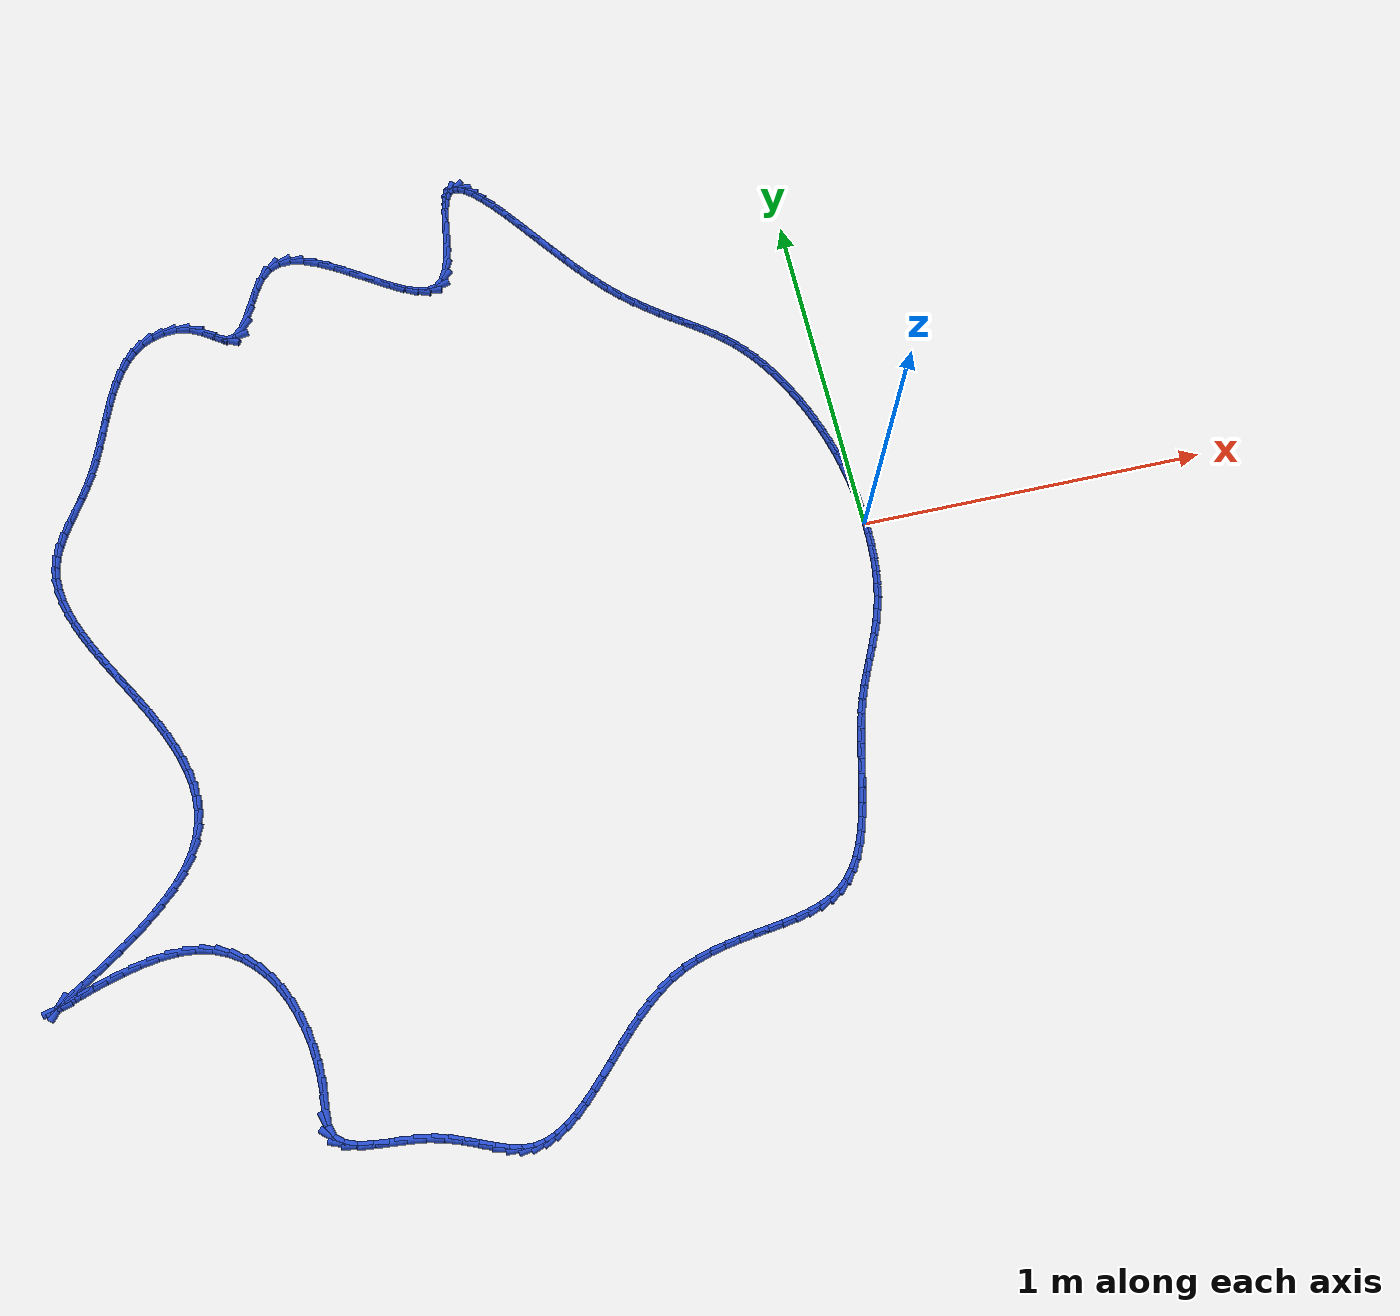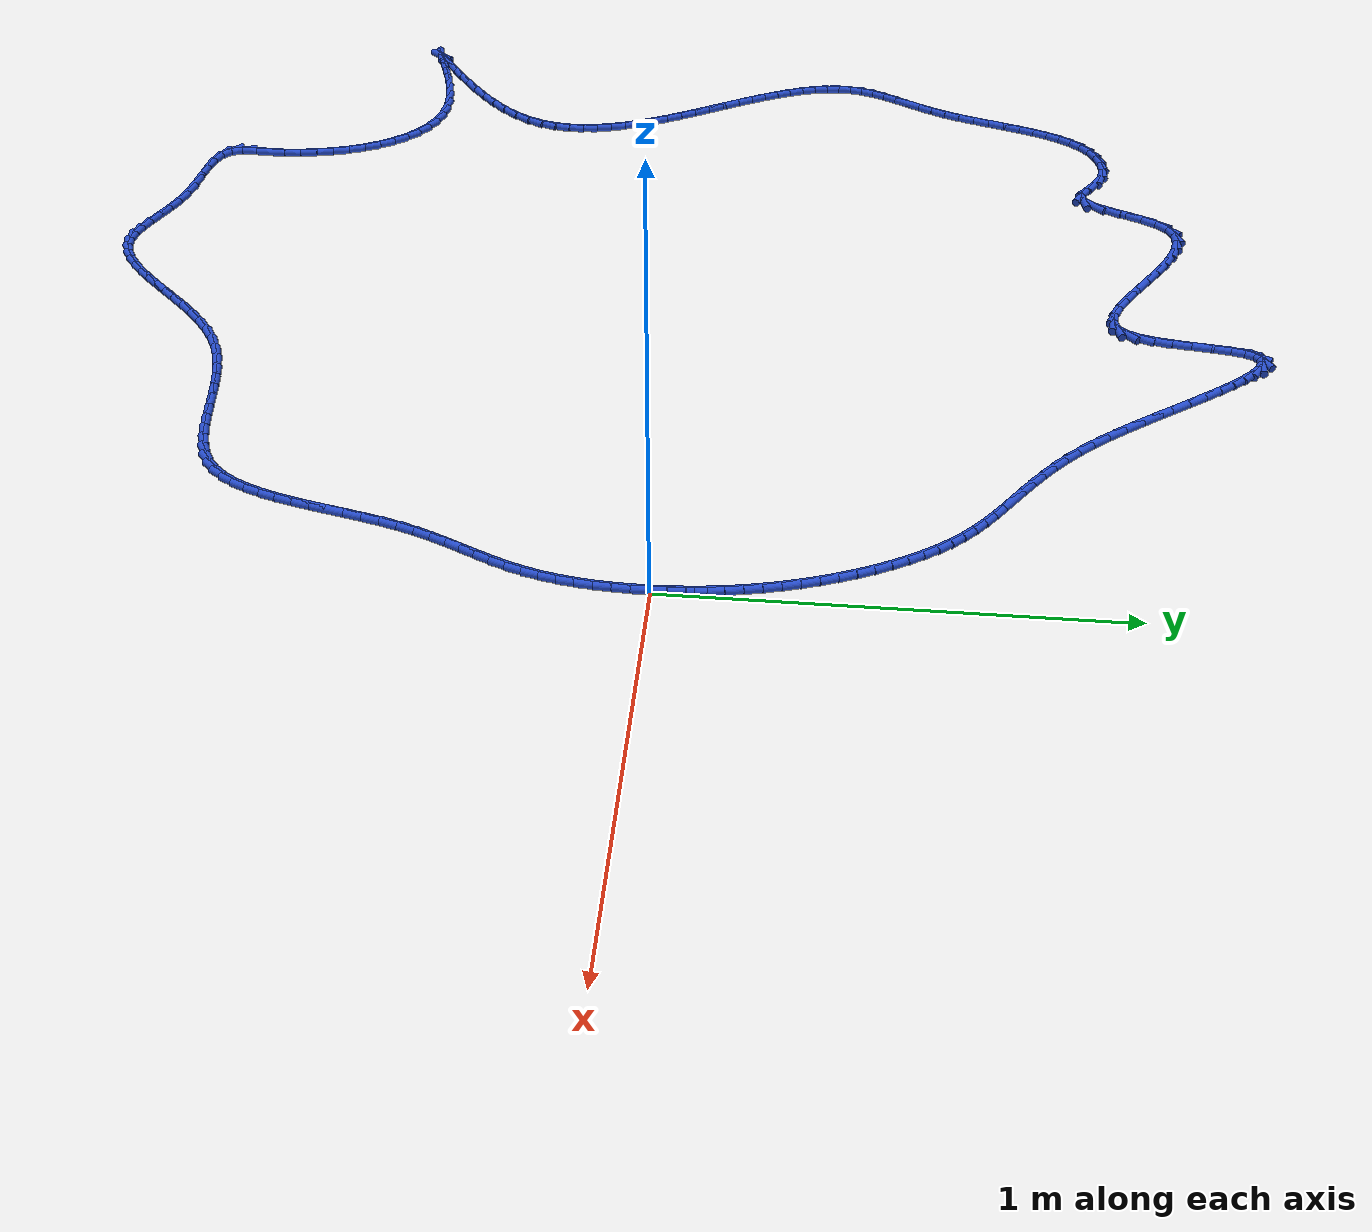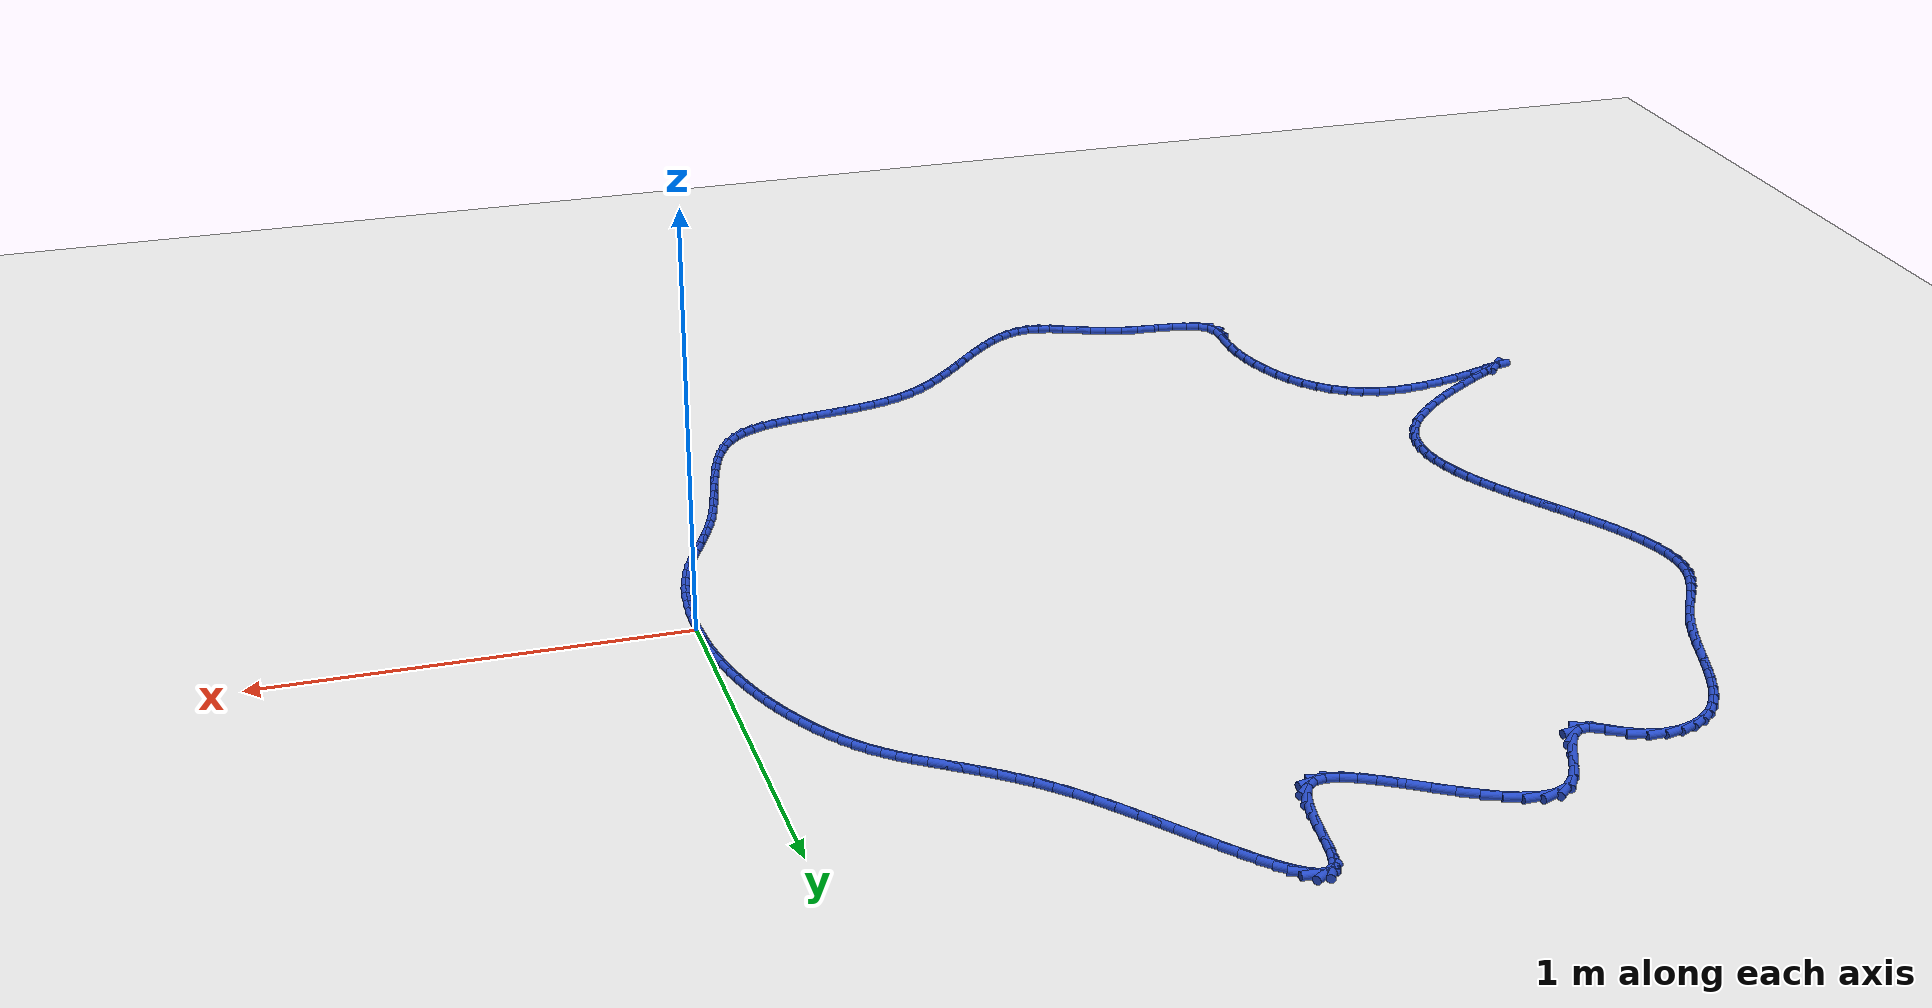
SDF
<sdf version="1.6">
 <world name="default">
  <light name="sun" type="directional">
   <pose>0 0 10 0 -0 0</pose>
   <diffuse>0.8 0.8 0.8 1</diffuse>
   <specular>0.2 0.2 0.2 1</specular>
   <attenuation>
    <range>1000</range>
    <constant>0.9</constant>
    <linear>0.01</linear>
    <quadratic>0.001</quadratic>
   </attenuation>
   <direction>-0.5 0.1 -0.9</direction>
  </light>
  <model name="ground_plane">
   <static>1</static>
   <link name="link">
    <collision name="collision">
     <geometry><plane><normal>0 0 1</normal><size>100 100</size></plane></geometry>
     <surface><friction><ode><mu>100</mu><mu2>50</mu2></ode></friction></surface>
    </collision>
    <visual name="visual">
     <cast_shadows>0</cast_shadows>
     <geometry><plane><normal>0 0 1</normal><size>100 100</size></plane></geometry>
     <material>
      <script><uri>file://media/materials/scripts/gazebo.material</uri><name>Gazebo/WhiteGlow</name></script>
     </material>
    </visual>
   </link>
  </model>
  <gravity>0 0 -9.8</gravity>
  <magnetic_field>6e-06 2.3e-05 -4.2e-05</magnetic_field>
  <atmosphere type="adiabatic"/>
  <physics name="default_physics" default="0" type="ode">
   <max_step_size>0.001</max_step_size>
   <real_time_factor>1</real_time_factor>
   <real_time_update_rate>1000</real_time_update_rate>
  </physics>
  <scene><ambient>0.4 0.4 0.4 1</ambient><background>0.7 0.7 0.7 1</background><shadows>1</shadows></scene>
  <spherical_coordinates>
   <surface_model>EARTH_WGS84</surface_model>
   <latitude_deg>0</latitude_deg>
   <longitude_deg>0</longitude_deg>
   <elevation>0</elevation>
   <heading_deg>0</heading_deg>
  </spherical_coordinates>
  <model name="line">
   <link name="link_0">
    <pose>-2.6020852139652106e-18 7.632783294297951e-17 0.01 0 1.57 -1.5426805723043262</pose>
    <collision name="collision">
     <geometry><cylinder><radius>0.01</radius><length>0.08</length></cylinder></geometry>
    </collision>
    <visual name="visual">
     <material>
      <script><name>Gazebo/Blue</name><uri>file://media/materials/scripts/gazebo.material</uri></script>
     </material>
     <geometry><cylinder><radius>0.01</radius><length>0.08</length></cylinder></geometry>
    </visual>
   </link>
   <link name="link_1">
    <pose>-0.0010803555094937593 0.03841514631031116 0.01 0 1.57 -1.5085308011320138</pose>
    <collision name="collision">
     <geometry><cylinder><radius>0.01</radius><length>0.08</length></cylinder></geometry>
    </collision>
    <visual name="visual">
     <material>
      <script><name>Gazebo/Blue</name><uri>file://media/materials/scripts/gazebo.material</uri></script>
     </material>
     <geometry><cylinder><radius>0.01</radius><length>0.08</length></cylinder></geometry>
    </visual>
   </link>
   <link name="link_2">
    <pose>-0.0034599829773963036 0.07658315949222319 0.01 0 1.57 -1.473365610789837</pose>
    <collision name="collision">
     <geometry><cylinder><radius>0.01</radius><length>0.08</length></cylinder></geometry>
    </collision>
    <visual name="visual">
     <material>
      <script><name>Gazebo/Blue</name><uri>file://media/materials/scripts/gazebo.material</uri></script>
     </material>
     <geometry><cylinder><radius>0.01</radius><length>0.08</length></cylinder></geometry>
    </visual>
   </link>
   <link name="link_3">
    <pose>-0.007172297588708049 0.11456461583194613 0.01 0 1.57 -1.4374397576351434</pose>
    <collision name="collision">
     <geometry><cylinder><radius>0.01</radius><length>0.08</length></cylinder></geometry>
    </collision>
    <visual name="visual">
     <material>
      <script><name>Gazebo/Blue</name><uri>file://media/materials/scripts/gazebo.material</uri></script>
     </material>
     <geometry><cylinder><radius>0.01</radius><length>0.08</length></cylinder></geometry>
    </visual>
   </link>
   <link name="link_4">
    <pose>-0.012250714528429432 0.15242009161568984 0.01 0 1.57 -1.401027397693487</pose>
    <collision name="collision">
     <geometry><cylinder><radius>0.01</radius><length>0.08</length></cylinder></geometry>
    </collision>
    <visual name="visual">
     <material>
      <script><name>Gazebo/Blue</name><uri>file://media/materials/scripts/gazebo.material</uri></script>
     </material>
     <geometry><cylinder><radius>0.01</radius><length>0.08</length></cylinder></geometry>
    </visual>
   </link>
   <link name="link_5">
    <pose>-0.018728648981560868 0.19021016312966432 0.01 0 1.57 -1.3644134127711403</pose>
    <collision name="collision">
     <geometry><cylinder><radius>0.01</radius><length>0.08</length></cylinder></geometry>
    </collision>
    <visual name="visual">
     <material>
      <script><name>Gazebo/Blue</name><uri>file://media/materials/scripts/gazebo.material</uri></script>
     </material>
     <geometry><cylinder><radius>0.01</radius><length>0.08</length></cylinder></geometry>
    </visual>
   </link>
   <link name="link_6">
    <pose>-0.026639516133102795 0.2279954066600795 0.01 0 1.57 -1.3278839121284285</pose>
    <collision name="collision">
     <geometry><cylinder><radius>0.01</radius><length>0.08</length></cylinder></geometry>
    </collision>
    <visual name="visual">
     <material>
      <script><name>Gazebo/Blue</name><uri>file://media/materials/scripts/gazebo.material</uri></script>
     </material>
     <geometry><cylinder><radius>0.01</radius><length>0.08</length></cylinder></geometry>
    </visual>
   </link>
   <link name="link_7">
    <pose>-0.03601673116805562 0.2658363984931452 0.01 0 1.57 -1.2916774704146423</pose>
    <collision name="collision">
     <geometry><cylinder><radius>0.01</radius><length>0.08</length></cylinder></geometry>
    </collision>
    <visual name="visual">
     <material>
      <script><name>Gazebo/Blue</name><uri>file://media/materials/scripts/gazebo.material</uri></script>
     </material>
     <geometry><cylinder><radius>0.01</radius><length>0.08</length></cylinder></geometry>
    </visual>
   </link>
   <link name="link_8">
    <pose>-0.046885220975244425 0.303758479511365 0.01 0 1.57 -1.2555684967018743</pose>
    <collision name="collision">
     <geometry><cylinder><radius>0.01</radius><length>0.08</length></cylinder></geometry>
    </collision>
    <visual name="visual">
     <material>
      <script><name>Gazebo/Blue</name><uri>file://media/materials/scripts/gazebo.material</uri></script>
     </material>
     <geometry><cylinder><radius>0.01</radius><length>0.08</length></cylinder></geometry>
    </visual>
   </link>
   <link name="link_9">
    <pose>-0.05922336456998789 0.3415937677076539 0.01 0 1.57 -1.2190013547056364</pose>
    <collision name="collision">
     <geometry><cylinder><radius>0.01</radius><length>0.08</length></cylinder></geometry>
    </collision>
    <visual name="visual">
     <material>
      <script><name>Gazebo/Blue</name><uri>file://media/materials/scripts/gazebo.material</uri></script>
     </material>
     <geometry><cylinder><radius>0.01</radius><length>0.08</length></cylinder></geometry>
    </visual>
   </link>
   <link name="link_10">
    <pose>-0.07299366760217361 0.3791084898256602 0.01 0 1.57 -1.1814392259046531</pose>
    <collision name="collision">
     <geometry><cylinder><radius>0.01</radius><length>0.08</length></cylinder></geometry>
    </collision>
    <visual name="visual">
     <material>
      <script><name>Gazebo/Blue</name><uri>file://media/materials/scripts/gazebo.material</uri></script>
     </material>
     <geometry><cylinder><radius>0.01</radius><length>0.08</length></cylinder></geometry>
    </visual>
   </link>
   <link name="link_11">
    <pose>-0.08815862222926604 0.4160688166012099 0.01 0 1.57 -1.1423320725947321</pose>
    <collision name="collision">
     <geometry><cylinder><radius>0.01</radius><length>0.08</length></cylinder></geometry>
    </collision>
    <visual name="visual">
     <material>
      <script><name>Gazebo/Blue</name><uri>file://media/materials/scripts/gazebo.material</uri></script>
     </material>
     <geometry><cylinder><radius>0.01</radius><length>0.08</length></cylinder></geometry>
    </visual>
   </link>
   <link name="link_12">
    <pose>-0.10468072060872946 0.45224091877012906 0.01 0 1.57 -1.1010969514178366</pose>
    <collision name="collision">
     <geometry><cylinder><radius>0.01</radius><length>0.08</length></cylinder></geometry>
    </collision>
    <visual name="visual">
     <material>
      <script><name>Gazebo/Blue</name><uri>file://media/materials/scripts/gazebo.material</uri></script>
     </material>
     <geometry><cylinder><radius>0.01</radius><length>0.08</length></cylinder></geometry>
    </visual>
   </link>
   <link name="link_13">
    <pose>-0.12252245489802817 0.4873909670682433 0.01 0 1.57 -1.0570990799317062</pose>
    <collision name="collision">
     <geometry><cylinder><radius>0.01</radius><length>0.08</length></cylinder></geometry>
    </collision>
    <visual name="visual">
     <material>
      <script><name>Gazebo/Blue</name><uri>file://media/materials/scripts/gazebo.material</uri></script>
     </material>
     <geometry><cylinder><radius>0.01</radius><length>0.08</length></cylinder></geometry>
    </visual>
   </link>
   <link name="link_14">
    <pose>-0.14164631725462662 0.5212851322313792 0.01 0 1.57 -1.0096335910440757</pose>
    <collision name="collision">
     <geometry><cylinder><radius>0.01</radius><length>0.08</length></cylinder></geometry>
    </collision>
    <visual name="visual">
     <material>
      <script><name>Gazebo/Blue</name><uri>file://media/materials/scripts/gazebo.material</uri></script>
     </material>
     <geometry><cylinder><radius>0.01</radius><length>0.08</length></cylinder></geometry>
    </visual>
   </link>
   <link name="link_15">
    <pose>-0.1620147998359891 0.5536895849953622 0.01 0 1.57 -0.957908965155284</pose>
    <collision name="collision">
     <geometry><cylinder><radius>0.01</radius><length>0.08</length></cylinder></geometry>
    </collision>
    <visual name="visual">
     <material>
      <script><name>Gazebo/Blue</name><uri>file://media/materials/scripts/gazebo.material</uri></script>
     </material>
     <geometry><cylinder><radius>0.01</radius><length>0.08</length></cylinder></geometry>
    </visual>
   </link>
   <link name="link_16">
    <pose>-0.1835903947995799 0.5843704960960185 0.01 0 1.57 -0.9010347579570639</pose>
    <collision name="collision">
     <geometry><cylinder><radius>0.01</radius><length>0.08</length></cylinder></geometry>
    </collision>
    <visual name="visual">
     <material>
      <script><name>Gazebo/Blue</name><uri>file://media/materials/scripts/gazebo.material</uri></script>
     </material>
     <geometry><cylinder><radius>0.01</radius><length>0.08</length></cylinder></geometry>
    </visual>
   </link>
   <link name="link_17">
    <pose>-0.2063355943028634 0.6130940362691741 0.01 0 1.57 -0.8380211762480144</pose>
    <collision name="collision">
     <geometry><cylinder><radius>0.01</radius><length>0.08</length></cylinder></geometry>
    </collision>
    <visual name="visual">
     <material>
      <script><name>Gazebo/Blue</name><uri>file://media/materials/scripts/gazebo.material</uri></script>
     </material>
     <geometry><cylinder><radius>0.01</radius><length>0.08</length></cylinder></geometry>
    </visual>
   </link>
   <link name="link_18">
    <pose>-0.230212887760983 0.63962649404409 0.01 0 1.57 -0.7714757591283742</pose>
    <collision name="collision">
     <geometry><cylinder><radius>0.01</radius><length>0.08</length></cylinder></geometry>
    </collision>
    <visual name="visual">
     <material>
      <script><name>Gazebo/Blue</name><uri>file://media/materials/scripts/gazebo.material</uri></script>
     </material>
     <geometry><cylinder><radius>0.01</radius><length>0.08</length></cylinder></geometry>
    </visual>
   </link>
   <link name="link_19">
    <pose>-0.2551807037122628 0.6639085885262989 0.01 0 1.57 -0.7131995504046776</pose>
    <collision name="collision">
     <geometry><cylinder><radius>0.01</radius><length>0.08</length></cylinder></geometry>
    </collision>
    <visual name="visual">
     <material>
      <script><name>Gazebo/Blue</name><uri>file://media/materials/scripts/gazebo.material</uri></script>
     </material>
     <geometry><cylinder><radius>0.01</radius><length>0.08</length></cylinder></geometry>
    </visual>
   </link>
   <link name="link_20">
    <pose>-0.28118526488789186 0.6864053260793336 0.01 0 1.57 -0.6676120803178384</pose>
    <collision name="collision">
     <geometry><cylinder><radius>0.01</radius><length>0.08</length></cylinder></geometry>
    </collision>
    <visual name="visual">
     <material>
      <script><name>Gazebo/Blue</name><uri>file://media/materials/scripts/gazebo.material</uri></script>
     </material>
     <geometry><cylinder><radius>0.01</radius><length>0.08</length></cylinder></geometry>
    </visual>
   </link>
   <link name="link_21">
    <pose>-0.30817051018676056 0.707679812615565 0.01 0 1.57 -0.6361908917310383</pose>
    <collision name="collision">
     <geometry><cylinder><radius>0.01</radius><length>0.08</length></cylinder></geometry>
    </collision>
    <visual name="visual">
     <material>
      <script><name>Gazebo/Blue</name><uri>file://media/materials/scripts/gazebo.material</uri></script>
     </material>
     <geometry><cylinder><radius>0.01</radius><length>0.08</length></cylinder></geometry>
    </visual>
   </link>
   <link name="link_22">
    <pose>-0.33608037850775985 0.7282951540473648 0.01 0 1.57 -0.6194041011593644</pose>
    <collision name="collision">
     <geometry><cylinder><radius>0.01</radius><length>0.08</length></cylinder></geometry>
    </collision>
    <visual name="visual">
     <material>
      <script><name>Gazebo/Blue</name><uri>file://media/materials/scripts/gazebo.material</uri></script>
     </material>
     <geometry><cylinder><radius>0.01</radius><length>0.08</length></cylinder></geometry>
    </visual>
   </link>
   <link name="link_23">
    <pose>-0.3648588087497804 0.7488144562871043 0.01 0 1.57 -0.6168846186867651</pose>
    <collision name="collision">
     <geometry><cylinder><radius>0.01</radius><length>0.08</length></cylinder></geometry>
    </collision>
    <visual name="visual">
     <material>
      <script><name>Gazebo/Blue</name><uri>file://media/materials/scripts/gazebo.material</uri></script>
     </material>
     <geometry><cylinder><radius>0.01</radius><length>0.08</length></cylinder></geometry>
    </visual>
   </link>
   <link name="link_24">
    <pose>-0.39444973981171283 0.769800825247155 0.01 0 1.57 -0.6276255746605878</pose>
    <collision name="collision">
     <geometry><cylinder><radius>0.01</radius><length>0.08</length></cylinder></geometry>
    </collision>
    <visual name="visual">
     <material>
      <script><name>Gazebo/Blue</name><uri>file://media/materials/scripts/gazebo.material</uri></script>
     </material>
     <geometry><cylinder><radius>0.01</radius><length>0.08</length></cylinder></geometry>
    </visual>
   </link>
   <link name="link_25">
    <pose>-0.42479711059244796 0.7918173668398883 0.01 0 1.57 -0.6501466335252065</pose>
    <collision name="collision">
     <geometry><cylinder><radius>0.01</radius><length>0.08</length></cylinder></geometry>
    </collision>
    <visual name="visual">
     <material>
      <script><name>Gazebo/Blue</name><uri>file://media/materials/scripts/gazebo.material</uri></script>
     </material>
     <geometry><cylinder><radius>0.01</radius><length>0.08</length></cylinder></geometry>
    </visual>
   </link>
   <link name="link_26">
    <pose>-0.4558448599908764 0.8154271869776759 0.01 0 1.57 -0.6826281856447373</pose>
    <collision name="collision">
     <geometry><cylinder><radius>0.01</radius><length>0.08</length></cylinder></geometry>
    </collision>
    <visual name="visual">
     <material>
      <script><name>Gazebo/Blue</name><uri>file://media/materials/scripts/gazebo.material</uri></script>
     </material>
     <geometry><cylinder><radius>0.01</radius><length>0.08</length></cylinder></geometry>
    </visual>
   </link>
   <link name="link_27">
    <pose>-0.4875369269058893 0.8411933915728894 0.01 0 1.57 -0.7230325928859175</pose>
    <collision name="collision">
     <geometry><cylinder><radius>0.01</radius><length>0.08</length></cylinder></geometry>
    </collision>
    <visual name="visual">
     <material>
      <script><name>Gazebo/Blue</name><uri>file://media/materials/scripts/gazebo.material</uri></script>
     </material>
     <geometry><cylinder><radius>0.01</radius><length>0.08</length></cylinder></geometry>
    </visual>
   </link>
   <link name="link_28">
    <pose>-0.5198172502363768 0.8696790865378997 0.01 0 1.57 -0.7692302582501211</pose>
    <collision name="collision">
     <geometry><cylinder><radius>0.01</radius><length>0.08</length></cylinder></geometry>
    </collision>
    <visual name="visual">
     <material>
      <script><name>Gazebo/Blue</name><uri>file://media/materials/scripts/gazebo.material</uri></script>
     </material>
     <geometry><cylinder><radius>0.01</radius><length>0.08</length></cylinder></geometry>
    </visual>
   </link>
   <link name="link_29">
    <pose>-0.5526297688812298 0.9014473777850786 0.01 0 1.57 -0.8190387754056678</pose>
    <collision name="collision">
     <geometry><cylinder><radius>0.01</radius><length>0.08</length></cylinder></geometry>
    </collision>
    <visual name="visual">
     <material>
      <script><name>Gazebo/Blue</name><uri>file://media/materials/scripts/gazebo.material</uri></script>
     </material>
     <geometry><cylinder><radius>0.01</radius><length>0.08</length></cylinder></geometry>
    </visual>
   </link>
   <link name="link_30">
    <pose>-0.5859174586925855 0.937053574789607 0.01 0 1.57 -0.8643724727050911</pose>
    <collision name="collision">
     <geometry><cylinder><radius>0.01</radius><length>0.08</length></cylinder></geometry>
    </collision>
    <visual name="visual">
     <material>
      <script><name>Gazebo/Blue</name><uri>file://media/materials/scripts/gazebo.material</uri></script>
     </material>
     <geometry><cylinder><radius>0.01</radius><length>0.08</length></cylinder></geometry>
    </visual>
   </link>
   <link name="link_31">
    <pose>-0.6195510498346447 0.9764681151437421 0.01 0 1.57 -0.8966434586433389</pose>
    <collision name="collision">
     <geometry><cylinder><radius>0.01</radius><length>0.08</length></cylinder></geometry>
    </collision>
    <visual name="visual">
     <material>
      <script><name>Gazebo/Blue</name><uri>file://media/materials/scripts/gazebo.material</uri></script>
     </material>
     <geometry><cylinder><radius>0.01</radius><length>0.08</length></cylinder></geometry>
    </visual>
   </link>
   <link name="link_32">
    <pose>-0.6532800736706355 1.018680259943836 0.01 0 1.57 -0.9181249196915459</pose>
    <collision name="collision">
     <geometry><cylinder><radius>0.01</radius><length>0.08</length></cylinder></geometry>
    </collision>
    <visual name="visual">
     <material>
      <script><name>Gazebo/Blue</name><uri>file://media/materials/scripts/gazebo.material</uri></script>
     </material>
     <geometry><cylinder><radius>0.01</radius><length>0.08</length></cylinder></geometry>
    </visual>
   </link>
   <link name="link_33">
    <pose>-0.6868424787102823 1.0625855001868465 0.01 0 1.57 -0.9307076820168094</pose>
    <collision name="collision">
     <geometry><cylinder><radius>0.01</radius><length>0.08</length></cylinder></geometry>
    </collision>
    <visual name="visual">
     <material>
      <script><name>Gazebo/Blue</name><uri>file://media/materials/scripts/gazebo.material</uri></script>
     </material>
     <geometry><cylinder><radius>0.01</radius><length>0.08</length></cylinder></geometry>
    </visual>
   </link>
   <link name="link_34">
    <pose>-0.7199762134633086 1.107079326869731 0.01 0 1.57 -0.9352062492344857</pose>
    <collision name="collision">
     <geometry><cylinder><radius>0.01</radius><length>0.08</length></cylinder></geometry>
    </collision>
    <visual name="visual">
     <material>
      <script><name>Gazebo/Blue</name><uri>file://media/materials/scripts/gazebo.material</uri></script>
     </material>
     <geometry><cylinder><radius>0.01</radius><length>0.08</length></cylinder></geometry>
    </visual>
   </link>
   <link name="link_35">
    <pose>-0.752419226439439 1.1510572309894462 0.01 0 1.57 -0.9315068500089022</pose>
    <collision name="collision">
     <geometry><cylinder><radius>0.01</radius><length>0.08</length></cylinder></geometry>
    </collision>
    <visual name="visual">
     <material>
      <script><name>Gazebo/Blue</name><uri>file://media/materials/scripts/gazebo.material</uri></script>
     </material>
     <geometry><cylinder><radius>0.01</radius><length>0.08</length></cylinder></geometry>
    </visual>
   </link>
   <link name="link_36">
    <pose>-0.7839094661483975 1.1934147035429505 0.01 0 1.57 -0.9184564366562011</pose>
    <collision name="collision">
     <geometry><cylinder><radius>0.01</radius><length>0.08</length></cylinder></geometry>
    </collision>
    <visual name="visual">
     <material>
      <script><name>Gazebo/Blue</name><uri>file://media/materials/scripts/gazebo.material</uri></script>
     </material>
     <geometry><cylinder><radius>0.01</radius><length>0.08</length></cylinder></geometry>
    </visual>
   </link>
   <link name="link_37">
    <pose>-0.814184881099908 1.233047235527201 0.01 0 1.57 -0.8934029825798333</pose>
    <collision name="collision">
     <geometry><cylinder><radius>0.01</radius><length>0.08</length></cylinder></geometry>
    </collision>
    <visual name="visual">
     <material>
      <script><name>Gazebo/Blue</name><uri>file://media/materials/scripts/gazebo.material</uri></script>
     </material>
     <geometry><cylinder><radius>0.01</radius><length>0.08</length></cylinder></geometry>
    </visual>
   </link>
   <link name="link_38">
    <pose>-0.8429834198036946 1.2688503179391553 0.01 0 1.57 -0.8510656682763901</pose>
    <collision name="collision">
     <geometry><cylinder><radius>0.01</radius><length>0.08</length></cylinder></geometry>
    </collision>
    <visual name="visual">
     <material>
      <script><name>Gazebo/Blue</name><uri>file://media/materials/scripts/gazebo.material</uri></script>
     </material>
     <geometry><cylinder><radius>0.01</radius><length>0.08</length></cylinder></geometry>
    </visual>
   </link>
   <link name="link_39">
    <pose>-0.8700430307694814 1.2997194417757705 0.01 0 1.57 -0.7808285673652635</pose>
    <collision name="collision">
     <geometry><cylinder><radius>0.01</radius><length>0.08</length></cylinder></geometry>
    </collision>
    <visual name="visual">
     <material>
      <script><name>Gazebo/Blue</name><uri>file://media/materials/scripts/gazebo.material</uri></script>
     </material>
     <geometry><cylinder><radius>0.01</radius><length>0.08</length></cylinder></geometry>
    </visual>
   </link>
   <link name="link_40">
    <pose>-0.8951016625069927 1.3245500980340046 0.01 0 1.57 -0.6598877897646162</pose>
    <collision name="collision">
     <geometry><cylinder><radius>0.01</radius><length>0.08</length></cylinder></geometry>
    </collision>
    <visual name="visual">
     <material>
      <script><name>Gazebo/Blue</name><uri>file://media/materials/scripts/gazebo.material</uri></script>
     </material>
     <geometry><cylinder><radius>0.01</radius><length>0.08</length></cylinder></geometry>
    </visual>
   </link>
   <link name="link_41">
    <pose>-0.9178972635259522 1.342237777710814 0.01 0 1.57 -0.43584172484073064</pose>
    <collision name="collision">
     <geometry><cylinder><radius>0.01</radius><length>0.08</length></cylinder></geometry>
    </collision>
    <visual name="visual">
     <material>
      <script><name>Gazebo/Blue</name><uri>file://media/materials/scripts/gazebo.material</uri></script>
     </material>
     <geometry><cylinder><radius>0.01</radius><length>0.08</length></cylinder></geometry>
    </visual>
   </link>
   <link name="link_42">
    <pose>-0.9381677823360841 1.3516779718031575 0.01 0 1.57 -0.0050447185182563034</pose>
    <collision name="collision">
     <geometry><cylinder><radius>0.01</radius><length>0.08</length></cylinder></geometry>
    </collision>
    <visual name="visual">
     <material>
      <script><name>Gazebo/Blue</name><uri>file://media/materials/scripts/gazebo.material</uri></script>
     </material>
     <geometry><cylinder><radius>0.01</radius><length>0.08</length></cylinder></geometry>
    </visual>
   </link>
   <link name="link_43">
    <pose>-0.9556511674471128 1.351766171307992 0.01 0 1.57 0.6229125261429215</pose>
    <collision name="collision">
     <geometry><cylinder><radius>0.01</radius><length>0.08</length></cylinder></geometry>
    </collision>
    <visual name="visual">
     <material>
      <script><name>Gazebo/Blue</name><uri>file://media/materials/scripts/gazebo.material</uri></script>
     </material>
     <geometry><cylinder><radius>0.01</radius><length>0.08</length></cylinder></geometry>
    </visual>
   </link>
   <link name="link_44">
    <pose>-0.9700853673687616 1.3413978672222746 0.01 0 1.57 1.0995372211359704</pose>
    <collision name="collision">
     <geometry><cylinder><radius>0.01</radius><length>0.08</length></cylinder></geometry>
    </collision>
    <visual name="visual">
     <material>
      <script><name>Gazebo/Blue</name><uri>file://media/materials/scripts/gazebo.material</uri></script>
     </material>
     <geometry><cylinder><radius>0.01</radius><length>0.08</length></cylinder></geometry>
    </visual>
   </link>
   <link name="link_45">
    <pose>-0.9812284907543273 1.3195293486762585 0.01 0 1.57 1.322700077362954</pose>
    <collision name="collision">
     <geometry><cylinder><radius>0.01</radius><length>0.08</length></cylinder></geometry>
    </collision>
    <visual name="visual">
     <material>
      <script><name>Gazebo/Blue</name><uri>file://media/materials/scripts/gazebo.material</uri></script>
     </material>
     <geometry><cylinder><radius>0.01</radius><length>0.08</length></cylinder></geometry>
    </visual>
   </link>
   <link name="link_46">
    <pose>-0.9894662387985999 1.287009572620604 0.01 0 1.57 1.4112634199327305</pose>
    <collision name="collision">
     <geometry><cylinder><radius>0.01</radius><length>0.08</length></cylinder></geometry>
    </collision>
    <visual name="visual">
     <material>
      <script><name>Gazebo/Blue</name><uri>file://media/materials/scripts/gazebo.material</uri></script>
     </material>
     <geometry><cylinder><radius>0.01</radius><length>0.08</length></cylinder></geometry>
    </visual>
   </link>
   <link name="link_47">
    <pose>-0.9959192518571268 1.2469038953535598 0.01 0 1.57 1.4405117028704824</pose>
    <collision name="collision">
     <geometry><cylinder><radius>0.01</radius><length>0.08</length></cylinder></geometry>
    </collision>
    <visual name="visual">
     <material>
      <script><name>Gazebo/Blue</name><uri>file://media/materials/scripts/gazebo.material</uri></script>
     </material>
     <geometry><cylinder><radius>0.01</radius><length>0.08</length></cylinder></geometry>
    </visual>
   </link>
   <link name="link_48">
    <pose>-1.0017499676841224 1.2024037240522543 0.01 0 1.57 1.4322927167606936</pose>
    <collision name="collision">
     <geometry><cylinder><radius>0.01</radius><length>0.08</length></cylinder></geometry>
    </collision>
    <visual name="visual">
     <material>
      <script><name>Gazebo/Blue</name><uri>file://media/materials/scripts/gazebo.material</uri></script>
     </material>
     <geometry><cylinder><radius>0.01</radius><length>0.08</length></cylinder></geometry>
    </visual>
   </link>
   <link name="link_49">
    <pose>-1.0081208240337995 1.156700465893815 0.01 0 1.57 1.3881704513991</pose>
    <collision name="collision">
     <geometry><cylinder><radius>0.01</radius><length>0.08</length></cylinder></geometry>
    </collision>
    <visual name="visual">
     <material>
      <script><name>Gazebo/Blue</name><uri>file://media/materials/scripts/gazebo.material</uri></script>
     </material>
     <geometry><cylinder><radius>0.01</radius><length>0.08</length></cylinder></geometry>
    </visual>
   </link>
   <link name="link_50">
    <pose>-1.016194258660373 1.112985528055369 0.01 0 1.57 1.2942155477918444</pose>
    <collision name="collision">
     <geometry><cylinder><radius>0.01</radius><length>0.08</length></cylinder></geometry>
    </collision>
    <visual name="visual">
     <material>
      <script><name>Gazebo/Blue</name><uri>file://media/materials/scripts/gazebo.material</uri></script>
     </material>
     <geometry><cylinder><radius>0.01</radius><length>0.08</length></cylinder></geometry>
    </visual>
   </link>
   <link name="link_51">
    <pose>-1.0271327093180562 1.0744503177140448 0.01 0 1.57 1.1102335037299869</pose>
    <collision name="collision">
     <geometry><cylinder><radius>0.01</radius><length>0.08</length></cylinder></geometry>
    </collision>
    <visual name="visual">
     <material>
      <script><name>Gazebo/Blue</name><uri>file://media/materials/scripts/gazebo.material</uri></script>
     </material>
     <geometry><cylinder><radius>0.01</radius><length>0.08</length></cylinder></geometry>
    </visual>
   </link>
   <link name="link_52">
    <pose>-1.0420986137610633 1.0442862420469694 0.01 0 1.57 0.7468468014623375</pose>
    <collision name="collision">
     <geometry><cylinder><radius>0.01</radius><length>0.08</length></cylinder></geometry>
    </collision>
    <visual name="visual">
     <material>
      <script><name>Gazebo/Blue</name><uri>file://media/materials/scripts/gazebo.material</uri></script>
     </material>
     <geometry><cylinder><radius>0.01</radius><length>0.08</length></cylinder></geometry>
    </visual>
   </link>
   <link name="link_53">
    <pose>-1.0622385724257855 1.0256422005637924 0.01 0 1.57 0.23064214458469398</pose>
    <collision name="collision">
     <geometry><cylinder><radius>0.01</radius><length>0.08</length></cylinder></geometry>
    </collision>
    <visual name="visual">
     <material>
      <script><name>Gazebo/Blue</name><uri>file://media/materials/scripts/gazebo.material</uri></script>
     </material>
     <geometry><cylinder><radius>0.01</radius><length>0.08</length></cylinder></geometry>
    </visual>
   </link>
   <link name="link_54">
    <pose>-1.0879323075280776 1.0196087767915776 0.01 0 1.57 -0.15375915579281801</pose>
    <collision name="collision">
     <geometry><cylinder><radius>0.01</radius><length>0.08</length></cylinder></geometry>
    </collision>
    <visual name="visual">
     <material>
      <script><name>Gazebo/Blue</name><uri>file://media/materials/scripts/gazebo.material</uri></script>
     </material>
     <geometry><cylinder><radius>0.01</radius><length>0.08</length></cylinder></geometry>
    </visual>
   </link>
   <link name="link_55">
    <pose>-1.1184658002313381 1.0243409321093184 0.01 0 1.57 -0.3704330861370325</pose>
    <collision name="collision">
     <geometry><cylinder><radius>0.01</radius><length>0.08</length></cylinder></geometry>
    </collision>
    <visual name="visual">
     <material>
      <script><name>Gazebo/Blue</name><uri>file://media/materials/scripts/gazebo.material</uri></script>
     </material>
     <geometry><cylinder><radius>0.01</radius><length>0.08</length></cylinder></geometry>
    </visual>
   </link>
   <link name="link_56">
    <pose>-1.153041227740167 1.0377686964490336 0.01 0 1.57 -0.4875453235978983</pose>
    <collision name="collision">
     <geometry><cylinder><radius>0.01</radius><length>0.08</length></cylinder></geometry>
    </collision>
    <visual name="visual">
     <material>
      <script><name>Gazebo/Blue</name><uri>file://media/materials/scripts/gazebo.material</uri></script>
     </material>
     <geometry><cylinder><radius>0.01</radius><length>0.08</length></cylinder></geometry>
    </visual>
   </link>
   <link name="link_57">
    <pose>-1.1908607672591642 1.0578220997427414 0.01 0 1.57 -0.5485887633398006</pose>
    <collision name="collision">
     <geometry><cylinder><radius>0.01</radius><length>0.08</length></cylinder></geometry>
    </collision>
    <visual name="visual">
     <material>
      <script><name>Gazebo/Blue</name><uri>file://media/materials/scripts/gazebo.material</uri></script>
     </material>
     <geometry><cylinder><radius>0.01</radius><length>0.08</length></cylinder></geometry>
    </visual>
   </link>
   <link name="link_58">
    <pose>-1.231126595992929 1.0824311719224593 0.01 0 1.57 -0.5738633636244629</pose>
    <collision name="collision">
     <geometry><cylinder><radius>0.01</radius><length>0.08</length></cylinder></geometry>
    </collision>
    <visual name="visual">
     <material>
      <script><name>Gazebo/Blue</name><uri>file://media/materials/scripts/gazebo.material</uri></script>
     </material>
     <geometry><cylinder><radius>0.01</radius><length>0.08</length></cylinder></geometry>
    </visual>
   </link>
   <link name="link_59">
    <pose>-1.273040891146062 1.1095259429202065 0.01 0 1.57 -0.5716477082837806</pose>
    <collision name="collision">
     <geometry><cylinder><radius>0.01</radius><length>0.08</length></cylinder></geometry>
    </collision>
    <visual name="visual">
     <material>
      <script><name>Gazebo/Blue</name><uri>file://media/materials/scripts/gazebo.material</uri></script>
     </material>
     <geometry><cylinder><radius>0.01</radius><length>0.08</length></cylinder></geometry>
    </visual>
   </link>
   <link name="link_60">
    <pose>-1.315805829923162 1.137036442668 0.01 0 1.57 -0.5432584840086693</pose>
    <collision name="collision">
     <geometry><cylinder><radius>0.01</radius><length>0.08</length></cylinder></geometry>
    </collision>
    <visual name="visual">
     <material>
      <script><name>Gazebo/Blue</name><uri>file://media/materials/scripts/gazebo.material</uri></script>
     </material>
     <geometry><cylinder><radius>0.01</radius><length>0.08</length></cylinder></geometry>
    </visual>
   </link>
   <link name="link_61">
    <pose>-1.3586235895288297 1.1628927010978583 0.01 0 1.57 -0.48426368201422776</pose>
    <collision name="collision">
     <geometry><cylinder><radius>0.01</radius><length>0.08</length></cylinder></geometry>
    </collision>
    <visual name="visual">
     <material>
      <script><name>Gazebo/Blue</name><uri>file://media/materials/scripts/gazebo.material</uri></script>
     </material>
     <geometry><cylinder><radius>0.01</radius><length>0.08</length></cylinder></geometry>
    </visual>
   </link>
   <link name="link_62">
    <pose>-1.400696347167664 1.1850247481417997 0.01 0 1.57 -0.38318122949823424</pose>
    <collision name="collision">
     <geometry><cylinder><radius>0.01</radius><length>0.08</length></cylinder></geometry>
    </collision>
    <visual name="visual">
     <material>
      <script><name>Gazebo/Blue</name><uri>file://media/materials/scripts/gazebo.material</uri></script>
     </material>
     <geometry><cylinder><radius>0.01</radius><length>0.08</length></cylinder></geometry>
    </visual>
   </link>
   <link name="link_63">
    <pose>-1.441226280044266 1.2013626137318427 0.01 0 1.57 -0.21834967871028302</pose>
    <collision name="collision">
     <geometry><cylinder><radius>0.01</radius><length>0.08</length></cylinder></geometry>
    </collision>
    <visual name="visual">
     <material>
      <script><name>Gazebo/Blue</name><uri>file://media/materials/scripts/gazebo.material</uri></script>
     </material>
     <geometry><cylinder><radius>0.01</radius><length>0.08</length></cylinder></geometry>
    </visual>
   </link>
   <link name="link_64">
    <pose>-1.4794155653632335 1.2098363278000046 0.01 0 1.57 0.041641351532768274</pose>
    <collision name="collision">
     <geometry><cylinder><radius>0.01</radius><length>0.08</length></cylinder></geometry>
    </collision>
    <visual name="visual">
     <material>
      <script><name>Gazebo/Blue</name><uri>file://media/materials/scripts/gazebo.material</uri></script>
     </material>
     <geometry><cylinder><radius>0.01</radius><length>0.08</length></cylinder></geometry>
    </visual>
   </link>
   <link name="link_65">
    <pose>-1.5144663803291676 1.2083759202783042 0.01 0 1.57 0.4084082158583317</pose>
    <collision name="collision">
     <geometry><cylinder><radius>0.01</radius><length>0.08</length></cylinder></geometry>
    </collision>
    <visual name="visual">
     <material>
      <script><name>Gazebo/Blue</name><uri>file://media/materials/scripts/gazebo.material</uri></script>
     </material>
     <geometry><cylinder><radius>0.01</radius><length>0.08</length></cylinder></geometry>
    </visual>
   </link>
   <link name="link_66">
    <pose>-1.5455809021466682 1.194911421098759 0.01 0 1.57 0.7965346572013756</pose>
    <collision name="collision">
     <geometry><cylinder><radius>0.01</radius><length>0.08</length></cylinder></geometry>
    </collision>
    <visual name="visual">
     <material>
      <script><name>Gazebo/Blue</name><uri>file://media/materials/scripts/gazebo.material</uri></script>
     </material>
     <geometry><cylinder><radius>0.01</radius><length>0.08</length></cylinder></geometry>
    </visual>
   </link>
   <link name="link_67">
    <pose>-1.5720892115207314 1.1678060182665602 0.01 0 1.57 1.0317862784901017</pose>
    <collision name="collision">
     <geometry><cylinder><radius>0.01</radius><length>0.08</length></cylinder></geometry>
    </collision>
    <visual name="visual">
     <material>
      <script><name>Gazebo/Blue</name><uri>file://media/materials/scripts/gazebo.material</uri></script>
     </material>
     <geometry><cylinder><radius>0.01</radius><length>0.08</length></cylinder></geometry>
    </visual>
   </link>
   <link name="link_68">
    <pose>-1.5946820088326186 1.130030775220034 0.01 0 1.57 1.1290605640430258</pose>
    <collision name="collision">
     <geometry><cylinder><radius>0.01</radius><length>0.08</length></cylinder></geometry>
    </collision>
    <visual name="visual">
     <material>
      <script><name>Gazebo/Blue</name><uri>file://media/materials/scripts/gazebo.material</uri></script>
     </material>
     <geometry><cylinder><radius>0.01</radius><length>0.08</length></cylinder></geometry>
    </visual>
   </link>
   <link name="link_69">
    <pose>-1.6148713574030957 1.0873383836340151 0.01 0 1.57 1.138220194868814</pose>
    <collision name="collision">
     <geometry><cylinder><radius>0.01</radius><length>0.08</length></cylinder></geometry>
    </collision>
    <visual name="visual">
     <material>
      <script><name>Gazebo/Blue</name><uri>file://media/materials/scripts/gazebo.material</uri></script>
     </material>
     <geometry><cylinder><radius>0.01</radius><length>0.08</length></cylinder></geometry>
    </visual>
   </link>
   <link name="link_70">
    <pose>-1.6341806832297099 1.0455200160315063 0.01 0 1.57 1.0545456623109377</pose>
    <collision name="collision">
     <geometry><cylinder><radius>0.01</radius><length>0.08</length></cylinder></geometry>
    </collision>
    <visual name="visual">
     <material>
      <script><name>Gazebo/Blue</name><uri>file://media/materials/scripts/gazebo.material</uri></script>
     </material>
     <geometry><cylinder><radius>0.01</radius><length>0.08</length></cylinder></geometry>
    </visual>
   </link>
   <link name="link_71">
    <pose>-1.6541334123100049 1.0103668449355117 0.01 0 1.57 0.798277652305264</pose>
    <collision name="collision">
     <geometry><cylinder><radius>0.01</radius><length>0.08</length></cylinder></geometry>
    </collision>
    <visual name="visual">
     <material>
      <script><name>Gazebo/Blue</name><uri>file://media/materials/scripts/gazebo.material</uri></script>
     </material>
     <geometry><cylinder><radius>0.01</radius><length>0.08</length></cylinder></geometry>
    </visual>
   </link>
   <link name="link_72">
    <pose>-1.6762529706415275 0.9876700428690336 0.01 0 1.57 0.17111370114996938</pose>
    <collision name="collision">
     <geometry><cylinder><radius>0.01</radius><length>0.08</length></cylinder></geometry>
    </collision>
    <visual name="visual">
     <material>
      <script><name>Gazebo/Blue</name><uri>file://media/materials/scripts/gazebo.material</uri></script>
     </material>
     <geometry><cylinder><radius>0.01</radius><length>0.08</length></cylinder></geometry>
    </visual>
   </link>
   <link name="link_73">
    <pose>-1.7020614315523686 0.9832102489607192 0.01 0 1.57 -0.4556743477530194</pose>
    <collision name="collision">
     <geometry><cylinder><radius>0.01</radius><length>0.08</length></cylinder></geometry>
    </collision>
    <visual name="visual">
     <material>
      <script><name>Gazebo/Blue</name><uri>file://media/materials/scripts/gazebo.material</uri></script>
     </material>
     <geometry><cylinder><radius>0.01</radius><length>0.08</length></cylinder></geometry>
    </visual>
   </link>
   <link name="link_74">
    <pose>-1.7324839044844975 0.9981194751247711 0.01 0 1.57 -0.5985790229823945</pose>
    <collision name="collision">
     <geometry><cylinder><radius>0.01</radius><length>0.08</length></cylinder></geometry>
    </collision>
    <visual name="visual">
     <material>
      <script><name>Gazebo/Blue</name><uri>file://media/materials/scripts/gazebo.material</uri></script>
     </material>
     <geometry><cylinder><radius>0.01</radius><length>0.08</length></cylinder></geometry>
    </visual>
   </link>
   <link name="link_75">
    <pose>-1.766913837302748 1.0216025064259013 0.01 0 1.57 -0.47738661372117364</pose>
    <collision name="collision">
     <geometry><cylinder><radius>0.01</radius><length>0.08</length></cylinder></geometry>
    </collision>
    <visual name="visual">
     <material>
      <script><name>Gazebo/Blue</name><uri>file://media/materials/scripts/gazebo.material</uri></script>
     </material>
     <geometry><cylinder><radius>0.01</radius><length>0.08</length></cylinder></geometry>
    </visual>
   </link>
   <link name="link_76">
    <pose>-1.804495347901011 1.0410431829433733 0.01 0 1.57 -0.19990754112329895</pose>
    <collision name="collision">
     <geometry><cylinder><radius>0.01</radius><length>0.08</length></cylinder></geometry>
    </collision>
    <visual name="visual">
     <material>
      <script><name>Gazebo/Blue</name><uri>file://media/materials/scripts/gazebo.material</uri></script>
     </material>
     <geometry><cylinder><radius>0.01</radius><length>0.08</length></cylinder></geometry>
    </visual>
   </link>
   <link name="link_77">
    <pose>-1.8438077189204876 1.049008411003956 0.01 0 1.57 0.053767625382339194</pose>
    <collision name="collision">
     <geometry><cylinder><radius>0.01</radius><length>0.08</length></cylinder></geometry>
    </collision>
    <visual name="visual">
     <material>
      <script><name>Gazebo/Blue</name><uri>file://media/materials/scripts/gazebo.material</uri></script>
     </material>
     <geometry><cylinder><radius>0.01</radius><length>0.08</length></cylinder></geometry>
    </visual>
   </link>
   <link name="link_78">
    <pose>-1.8824643877965028 1.0469279284645692 0.01 0 1.57 0.27005372441491277</pose>
    <collision name="collision">
     <geometry><cylinder><radius>0.01</radius><length>0.08</length></cylinder></geometry>
    </collision>
    <visual name="visual">
     <material>
      <script><name>Gazebo/Blue</name><uri>file://media/materials/scripts/gazebo.material</uri></script>
     </material>
     <geometry><cylinder><radius>0.01</radius><length>0.08</length></cylinder></geometry>
    </visual>
   </link>
   <link name="link_79">
    <pose>-1.9179997420239243 1.0370911746953775 0.01 0 1.57 0.4734905389199982</pose>
    <collision name="collision">
     <geometry><cylinder><radius>0.01</radius><length>0.08</length></cylinder></geometry>
    </collision>
    <visual name="visual">
     <material>
      <script><name>Gazebo/Blue</name><uri>file://media/materials/scripts/gazebo.material</uri></script>
     </material>
     <geometry><cylinder><radius>0.01</radius><length>0.08</length></cylinder></geometry>
    </visual>
   </link>
   <link name="link_80">
    <pose>-1.9490303865350185 1.0211921611513424 0.01 0 1.57 0.6681683856602351</pose>
    <collision name="collision">
     <geometry><cylinder><radius>0.01</radius><length>0.08</length></cylinder></geometry>
    </collision>
    <visual name="visual">
     <material>
      <script><name>Gazebo/Blue</name><uri>file://media/materials/scripts/gazebo.material</uri></script>
     </material>
     <geometry><cylinder><radius>0.01</radius><length>0.08</length></cylinder></geometry>
    </visual>
   </link>
   <link name="link_81">
    <pose>-1.975941452641117 0.9999518693412468 0.01 0 1.57 0.8383107403914253</pose>
    <collision name="collision">
     <geometry><cylinder><radius>0.01</radius><length>0.08</length></cylinder></geometry>
    </collision>
    <visual name="visual">
     <material>
      <script><name>Gazebo/Blue</name><uri>file://media/materials/scripts/gazebo.material</uri></script>
     </material>
     <geometry><cylinder><radius>0.01</radius><length>0.08</length></cylinder></geometry>
    </visual>
   </link>
   <link name="link_82">
    <pose>-1.9992813709518307 0.97400143472504 0.01 0 1.57 0.9759647227715307</pose>
    <collision name="collision">
     <geometry><cylinder><radius>0.01</radius><length>0.08</length></cylinder></geometry>
    </collision>
    <visual name="visual">
     <material>
      <script><name>Gazebo/Blue</name><uri>file://media/materials/scripts/gazebo.material</uri></script>
     </material>
     <geometry><cylinder><radius>0.01</radius><length>0.08</length></cylinder></geometry>
    </visual>
   </link>
   <link name="link_83">
    <pose>-2.019598572076773 0.9439719927626696 0.01 0 1.57 1.0811100374972755</pose>
    <collision name="collision">
     <geometry><cylinder><radius>0.01</radius><length>0.08</length></cylinder></geometry>
    </collision>
    <visual name="visual">
     <material>
      <script><name>Gazebo/Blue</name><uri>file://media/materials/scripts/gazebo.material</uri></script>
     </material>
     <geometry><cylinder><radius>0.01</radius><length>0.08</length></cylinder></geometry>
    </visual>
   </link>
   <link name="link_84">
    <pose>-2.037441486625556 0.9104946789140858 0.01 0 1.57 1.1574979156431469</pose>
    <collision name="collision">
     <geometry><cylinder><radius>0.01</radius><length>0.08</length></cylinder></geometry>
    </collision>
    <visual name="visual">
     <material>
      <script><name>Gazebo/Blue</name><uri>file://media/materials/scripts/gazebo.material</uri></script>
     </material>
     <geometry><cylinder><radius>0.01</radius><length>0.08</length></cylinder></geometry>
    </visual>
   </link>
   <link name="link_85">
    <pose>-2.053358545207792 0.8742006286392352 0.01 0 1.57 1.209527164599635</pose>
    <collision name="collision">
     <geometry><cylinder><radius>0.01</radius><length>0.08</length></cylinder></geometry>
    </collision>
    <visual name="visual">
     <material>
      <script><name>Gazebo/Blue</name><uri>file://media/materials/scripts/gazebo.material</uri></script>
     </material>
     <geometry><cylinder><radius>0.01</radius><length>0.08</length></cylinder></geometry>
    </visual>
   </link>
   <link name="link_86">
    <pose>-2.0678981784330954 0.8357209773980682 0.01 0 1.57 1.2408419794130134</pose>
    <collision name="collision">
     <geometry><cylinder><radius>0.01</radius><length>0.08</length></cylinder></geometry>
    </collision>
    <visual name="visual">
     <material>
      <script><name>Gazebo/Blue</name><uri>file://media/materials/scripts/gazebo.material</uri></script>
     </material>
     <geometry><cylinder><radius>0.01</radius><length>0.08</length></cylinder></geometry>
    </visual>
   </link>
   <link name="link_87">
    <pose>-2.0816088169110762 0.7956868606505323 0.01 0 1.57 1.2539409053647543</pose>
    <collision name="collision">
     <geometry><cylinder><radius>0.01</radius><length>0.08</length></cylinder></geometry>
    </collision>
    <visual name="visual">
     <material>
      <script><name>Gazebo/Blue</name><uri>file://media/materials/scripts/gazebo.material</uri></script>
     </material>
     <geometry><cylinder><radius>0.01</radius><length>0.08</length></cylinder></geometry>
    </visual>
   </link>
   <link name="link_88">
    <pose>-2.0950388912513485 0.7547294138565759 0.01 0 1.57 1.2501794386859513</pose>
    <collision name="collision">
     <geometry><cylinder><radius>0.01</radius><length>0.08</length></cylinder></geometry>
    </collision>
    <visual name="visual">
     <material>
      <script><name>Gazebo/Blue</name><uri>file://media/materials/scripts/gazebo.material</uri></script>
     </material>
     <geometry><cylinder><radius>0.01</radius><length>0.08</length></cylinder></geometry>
    </visual>
   </link>
   <link name="link_89">
    <pose>-2.1087368320635242 0.7134797724761484 0.01 0 1.57 1.2298708304703576</pose>
    <collision name="collision">
     <geometry><cylinder><radius>0.01</radius><length>0.08</length></cylinder></geometry>
    </collision>
    <visual name="visual">
     <material>
      <script><name>Gazebo/Blue</name><uri>file://media/materials/scripts/gazebo.material</uri></script>
     </material>
     <geometry><cylinder><radius>0.01</radius><length>0.08</length></cylinder></geometry>
    </visual>
   </link>
   <link name="link_90">
    <pose>-2.1232510699572167 0.6725690719691977 0.01 0 1.57 1.1923914682861734</pose>
    <collision name="collision">
     <geometry><cylinder><radius>0.01</radius><length>0.08</length></cylinder></geometry>
    </collision>
    <visual name="visual">
     <material>
      <script><name>Gazebo/Blue</name><uri>file://media/materials/scripts/gazebo.material</uri></script>
     </material>
     <geometry><cylinder><radius>0.01</radius><length>0.08</length></cylinder></geometry>
    </visual>
   </link>
   <link name="link_91">
    <pose>-2.139130035542037 0.632628447795673 0.01 0 1.57 1.1366343366151208</pose>
    <collision name="collision">
     <geometry><cylinder><radius>0.01</radius><length>0.08</length></cylinder></geometry>
    </collision>
    <visual name="visual">
     <material>
      <script><name>Gazebo/Blue</name><uri>file://media/materials/scripts/gazebo.material</uri></script>
     </material>
     <geometry><cylinder><radius>0.01</radius><length>0.08</length></cylinder></geometry>
    </visual>
   </link>
   <link name="link_92">
    <pose>-2.1569101457007522 0.5942818139172366 0.01 0 1.57 1.0788738891274638</pose>
    <collision name="collision">
     <geometry><cylinder><radius>0.01</radius><length>0.08</length></cylinder></geometry>
    </collision>
    <visual name="visual">
     <material>
      <script><name>Gazebo/Blue</name><uri>file://media/materials/scripts/gazebo.material</uri></script>
     </material>
     <geometry><cylinder><radius>0.01</radius><length>0.08</length></cylinder></geometry>
    </visual>
   </link>
   <link name="link_93">
    <pose>-2.176479058954072 0.5577631131018529 0.01 0 1.57 1.0461234089684404</pose>
    <collision name="collision">
     <geometry><cylinder><radius>0.01</radius><length>0.08</length></cylinder></geometry>
    </collision>
    <visual name="visual">
     <material>
      <script><name>Gazebo/Blue</name><uri>file://media/materials/scripts/gazebo.material</uri></script>
     </material>
     <geometry><cylinder><radius>0.01</radius><length>0.08</length></cylinder></geometry>
    </visual>
   </link>
   <link name="link_94">
    <pose>-2.1967582421894334 0.5227255065405398 0.01 0 1.57 1.0421132653548126</pose>
    <collision name="collision">
     <geometry><cylinder><radius>0.01</radius><length>0.08</length></cylinder></geometry>
    </collision>
    <visual name="visual">
     <material>
      <script><name>Gazebo/Blue</name><uri>file://media/materials/scripts/gazebo.material</uri></script>
     </material>
     <geometry><cylinder><radius>0.01</radius><length>0.08</length></cylinder></geometry>
    </visual>
   </link>
   <link name="link_95">
    <pose>-2.2165904875612408 0.4887748637339923 0.01 0 1.57 1.0694247133861268</pose>
    <collision name="collision">
     <geometry><cylinder><radius>0.01</radius><length>0.08</length></cylinder></geometry>
    </collision>
    <visual name="visual">
     <material>
      <script><name>Gazebo/Blue</name><uri>file://media/materials/scripts/gazebo.material</uri></script>
     </material>
     <geometry><cylinder><radius>0.01</radius><length>0.08</length></cylinder></geometry>
    </visual>
   </link>
   <link name="link_96">
    <pose>-2.2348185872239013 0.4555170541829038 0.01 0 1.57 1.1320328790445908</pose>
    <collision name="collision">
     <geometry><cylinder><radius>0.01</radius><length>0.08</length></cylinder></geometry>
    </collision>
    <visual name="visual">
     <material>
      <script><name>Gazebo/Blue</name><uri>file://media/materials/scripts/gazebo.material</uri></script>
     </material>
     <geometry><cylinder><radius>0.01</radius><length>0.08</length></cylinder></geometry>
    </visual>
   </link>
   <link name="link_97">
    <pose>-2.250285333331819 0.42255794738796915 0.01 0 1.57 1.2346849685255605</pose>
    <collision name="collision">
     <geometry><cylinder><radius>0.01</radius><length>0.08</length></cylinder></geometry>
    </collision>
    <visual name="visual">
     <material>
      <script><name>Gazebo/Blue</name><uri>file://media/materials/scripts/gazebo.material</uri></script>
     </material>
     <geometry><cylinder><radius>0.01</radius><length>0.08</length></cylinder></geometry>
    </visual>
   </link>
   <link name="link_98">
    <pose>-2.261833518039401 0.38950341284988205 0.01 0 1.57 1.37721544960513</pose>
    <collision name="collision">
     <geometry><cylinder><radius>0.01</radius><length>0.08</length></cylinder></geometry>
    </collision>
    <visual name="visual">
     <material>
      <script><name>Gazebo/Blue</name><uri>file://media/materials/scripts/gazebo.material</uri></script>
     </material>
     <geometry><cylinder><radius>0.01</radius><length>0.08</length></cylinder></geometry>
    </visual>
   </link>
   <link name="link_99">
    <pose>-2.268404277793017 0.35598523952294214 0.01 0 1.57 1.5266387335055462</pose>
    <collision name="collision">
     <geometry><cylinder><radius>0.01</radius><length>0.08</length></cylinder></geometry>
    </collision>
    <visual name="visual">
     <material>
      <script><name>Gazebo/Blue</name><uri>file://media/materials/scripts/gazebo.material</uri></script>
     </material>
     <geometry><cylinder><radius>0.01</radius><length>0.08</length></cylinder></geometry>
    </visual>
   </link>
   <link name="link_100">
    <pose>-2.2699107590817555 0.3218913976679961 0.01 0 1.57 -1.481807915594717</pose>
    <collision name="collision">
     <geometry><cylinder><radius>0.01</radius><length>0.08</length></cylinder></geometry>
    </collision>
    <visual name="visual">
     <material>
      <script><name>Gazebo/Blue</name><uri>file://media/materials/scripts/gazebo.material</uri></script>
     </material>
     <geometry><cylinder><radius>0.01</radius><length>0.08</length></cylinder></geometry>
    </visual>
   </link>
   <link name="link_101">
    <pose>-2.2668204446412354 0.28725595746014987 0.01 0 1.57 -1.368346243201321</pose>
    <collision name="collision">
     <geometry><cylinder><radius>0.01</radius><length>0.08</length></cylinder></geometry>
    </collision>
    <visual name="visual">
     <material>
      <script><name>Gazebo/Blue</name><uri>file://media/materials/scripts/gazebo.material</uri></script>
     </material>
     <geometry><cylinder><radius>0.01</radius><length>0.08</length></cylinder></geometry>
    </visual>
   </link>
   <link name="link_102">
    <pose>-2.259607275632391 0.2521146912460552 0.01 0 1.57 -1.274742530770553</pose>
    <collision name="collision">
     <geometry><cylinder><radius>0.01</radius><length>0.08</length></cylinder></geometry>
    </collision>
    <visual name="visual">
     <material>
      <script><name>Gazebo/Blue</name><uri>file://media/materials/scripts/gazebo.material</uri></script>
     </material>
     <geometry><cylinder><radius>0.01</radius><length>0.08</length></cylinder></geometry>
    </visual>
   </link>
   <link name="link_103">
    <pose>-2.2487451932161577 0.21650337137236214 0.01 0 1.57 -1.199439524915591</pose>
    <collision name="collision">
     <geometry><cylinder><radius>0.01</radius><length>0.08</length></cylinder></geometry>
    </collision>
    <visual name="visual">
     <material>
      <script><name>Gazebo/Blue</name><uri>file://media/materials/scripts/gazebo.material</uri></script>
     </material>
     <geometry><cylinder><radius>0.01</radius><length>0.08</length></cylinder></geometry>
    </visual>
   </link>
   <link name="link_104">
    <pose>-2.2347081385534695 0.18045777018572284 0.01 0 1.57 -1.1402512146313977</pose>
    <collision name="collision">
     <geometry><cylinder><radius>0.01</radius><length>0.08</length></cylinder></geometry>
    </collision>
    <visual name="visual">
     <material>
      <script><name>Gazebo/Blue</name><uri>file://media/materials/scripts/gazebo.material</uri></script>
     </material>
     <geometry><cylinder><radius>0.01</radius><length>0.08</length></cylinder></geometry>
    </visual>
   </link>
   <link name="link_105">
    <pose>-2.21797005280526 0.14401366003278715 0.01 0 1.57 -1.0950136654537983</pose>
    <collision name="collision">
     <geometry><cylinder><radius>0.01</radius><length>0.08</length></cylinder></geometry>
    </collision>
    <visual name="visual">
     <material>
      <script><name>Gazebo/Blue</name><uri>file://media/materials/scripts/gazebo.material</uri></script>
     </material>
     <geometry><cylinder><radius>0.01</radius><length>0.08</length></cylinder></geometry>
    </visual>
   </link>
   <link name="link_106">
    <pose>-2.199004877132464 0.10720681326020703 0.01 0 1.57 -1.06187993469689</pose>
    <collision name="collision">
     <geometry><cylinder><radius>0.01</radius><length>0.08</length></cylinder></geometry>
    </collision>
    <visual name="visual">
     <material>
      <script><name>Gazebo/Blue</name><uri>file://media/materials/scripts/gazebo.material</uri></script>
     </material>
     <geometry><cylinder><radius>0.01</radius><length>0.08</length></cylinder></geometry>
    </visual>
   </link>
   <link name="link_107">
    <pose>-2.1782865526960165 0.07007300221463306 0.01 0 1.57 -1.0394132837308487</pose>
    <collision name="collision">
     <geometry><cylinder><radius>0.01</radius><length>0.08</length></cylinder></geometry>
    </collision>
    <visual name="visual">
     <material>
      <script><name>Gazebo/Blue</name><uri>file://media/materials/scripts/gazebo.material</uri></script>
     </material>
     <geometry><cylinder><radius>0.01</radius><length>0.08</length></cylinder></geometry>
    </visual>
   </link>
   <link name="link_108">
    <pose>-2.156289020656851 0.032647999242715685 0.01 0 1.57 -1.0265891306665724</pose>
    <collision name="collision">
     <geometry><cylinder><radius>0.01</radius><length>0.08</length></cylinder></geometry>
    </collision>
    <visual name="visual">
     <material>
      <script><name>Gazebo/Blue</name><uri>file://media/materials/scripts/gazebo.material</uri></script>
     </material>
     <geometry><cylinder><radius>0.01</radius><length>0.08</length></cylinder></geometry>
    </visual>
   </link>
   <link name="link_109">
    <pose>-2.133486222175902 -0.005032423308893051 0.01 0 1.57 -1.0227663564151037</pose>
    <collision name="collision">
     <geometry><cylinder><radius>0.01</radius><length>0.08</length></cylinder></geometry>
    </collision>
    <visual name="visual">
     <material>
      <script><name>Gazebo/Blue</name><uri>file://media/materials/scripts/gazebo.material</uri></script>
     </material>
     <geometry><cylinder><radius>0.01</radius><length>0.08</length></cylinder></geometry>
    </visual>
   </link>
   <link name="link_110">
    <pose>-2.1103520984141046 -0.04293249309354316 0.01 0 1.57 -1.0276562432326881</pose>
    <collision name="collision">
     <geometry><cylinder><radius>0.01</radius><length>0.08</length></cylinder></geometry>
    </collision>
    <visual name="visual">
     <material>
      <script><name>Gazebo/Blue</name><uri>file://media/materials/scripts/gazebo.material</uri></script>
     </material>
     <geometry><cylinder><radius>0.01</radius><length>0.08</length></cylinder></geometry>
    </visual>
   </link>
   <link name="link_111">
    <pose>-2.087360590532392 -0.08101643776458273 0.01 0 1.57 -1.041299931814616</pose>
    <collision name="collision">
     <geometry><cylinder><radius>0.01</radius><length>0.08</length></cylinder></geometry>
    </collision>
    <visual name="visual">
     <material>
      <script><name>Gazebo/Blue</name><uri>file://media/materials/scripts/gazebo.material</uri></script>
     </material>
     <geometry><cylinder><radius>0.01</radius><length>0.08</length></cylinder></geometry>
    </visual>
   </link>
   <link name="link_112">
    <pose>-2.0649856396917006 -0.1192484849753617 0.01 0 1.57 -1.0640561956062435</pose>
    <collision name="collision">
     <geometry><cylinder><radius>0.01</radius><length>0.08</length></cylinder></geometry>
    </collision>
    <visual name="visual">
     <material>
      <script><name>Gazebo/Blue</name><uri>file://media/materials/scripts/gazebo.material</uri></script>
     </material>
     <geometry><cylinder><radius>0.01</radius><length>0.08</length></cylinder></geometry>
    </visual>
   </link>
   <link name="link_113">
    <pose>-2.043701187052963 -0.15759286237922807 0.01 0 1.57 -1.0965953459257</pose>
    <collision name="collision">
     <geometry><cylinder><radius>0.01</radius><length>0.08</length></cylinder></geometry>
    </collision>
    <visual name="visual">
     <material>
      <script><name>Gazebo/Blue</name><uri>file://media/materials/scripts/gazebo.material</uri></script>
     </material>
     <geometry><cylinder><radius>0.01</radius><length>0.08</length></cylinder></geometry>
    </visual>
   </link>
   <link name="link_114">
    <pose>-2.0239811737771136 -0.19601379762953183 0.01 0 1.57 -1.1398884848863273</pose>
    <collision name="collision">
     <geometry><cylinder><radius>0.01</radius><length>0.08</length></cylinder></geometry>
    </collision>
    <visual name="visual">
     <material>
      <script><name>Gazebo/Blue</name><uri>file://media/materials/scripts/gazebo.material</uri></script>
     </material>
     <geometry><cylinder><radius>0.01</radius><length>0.08</length></cylinder></geometry>
    </visual>
   </link>
   <link name="link_115">
    <pose>-2.0062995410250877 -0.234475518379621 0.01 0 1.57 -1.1951711310356492</pose>
    <collision name="collision">
     <geometry><cylinder><radius>0.01</radius><length>0.08</length></cylinder></geometry>
    </collision>
    <visual name="visual">
     <material>
      <script><name>Gazebo/Blue</name><uri>file://media/materials/scripts/gazebo.material</uri></script>
     </material>
     <geometry><cylinder><radius>0.01</radius><length>0.08</length></cylinder></geometry>
    </visual>
   </link>
   <link name="link_116">
    <pose>-1.9911302299578197 -0.27294225228284524 0.01 0 1.57 -1.2638444069199752</pose>
    <collision name="collision">
     <geometry><cylinder><radius>0.01</radius><length>0.08</length></cylinder></geometry>
    </collision>
    <visual name="visual">
     <material>
      <script><name>Gazebo/Blue</name><uri>file://media/materials/scripts/gazebo.material</uri></script>
     </material>
     <geometry><cylinder><radius>0.01</radius><length>0.08</length></cylinder></geometry>
    </visual>
   </link>
   <link name="link_117">
    <pose>-1.9789471817362432 -0.3113782269925543 0.01 0 1.57 -1.3472573687049134</pose>
    <collision name="collision">
     <geometry><cylinder><radius>0.01</radius><length>0.08</length></cylinder></geometry>
    </collision>
    <visual name="visual">
     <material>
      <script><name>Gazebo/Blue</name><uri>file://media/materials/scripts/gazebo.material</uri></script>
     </material>
     <geometry><cylinder><radius>0.01</radius><length>0.08</length></cylinder></geometry>
    </visual>
   </link>
   <link name="link_118">
    <pose>-1.9702243375212938 -0.3497476701620954 0.01 0 1.57 -1.4463047945458527</pose>
    <collision name="collision">
     <geometry><cylinder><radius>0.01</radius><length>0.08</length></cylinder></geometry>
    </collision>
    <visual name="visual">
     <material>
      <script><name>Gazebo/Blue</name><uri>file://media/materials/scripts/gazebo.material</uri></script>
     </material>
     <geometry><cylinder><radius>0.01</radius><length>0.08</length></cylinder></geometry>
    </visual>
   </link>
   <link name="link_119">
    <pose>-1.9654356384739042 -0.38801480944481836 0.01 0 1.57 -1.5608144377266686</pose>
    <collision name="collision">
     <geometry><cylinder><radius>0.01</radius><length>0.08</length></cylinder></geometry>
    </collision>
    <visual name="visual">
     <material>
      <script><name>Gazebo/Blue</name><uri>file://media/materials/scripts/gazebo.material</uri></script>
     </material>
     <geometry><cylinder><radius>0.01</radius><length>0.08</length></cylinder></geometry>
    </visual>
   </link>
   <link name="link_120">
    <pose>-1.96505502575501 -0.42614387249407226 0.01 0 1.57 1.4527496686229517</pose>
    <collision name="collision">
     <geometry><cylinder><radius>0.01</radius><length>0.08</length></cylinder></geometry>
    </collision>
    <visual name="visual">
     <material>
      <script><name>Gazebo/Blue</name><uri>file://media/materials/scripts/gazebo.material</uri></script>
     </material>
     <geometry><cylinder><radius>0.01</radius><length>0.08</length></cylinder></geometry>
    </visual>
   </link>
   <link name="link_121">
    <pose>-1.9695564405255448 -0.4640990869632061 0.01 0 1.57 1.3153483702381141</pose>
    <collision name="collision">
     <geometry><cylinder><radius>0.01</radius><length>0.08</length></cylinder></geometry>
    </collision>
    <visual name="visual">
     <material>
      <script><name>Gazebo/Blue</name><uri>file://media/materials/scripts/gazebo.material</uri></script>
     </material>
     <geometry><cylinder><radius>0.01</radius><length>0.08</length></cylinder></geometry>
    </visual>
   </link>
   <link name="link_122">
    <pose>-1.979413823946444 -0.50184468050557 0.01 0 1.57 1.174592523456006</pose>
    <collision name="collision">
     <geometry><cylinder><radius>0.01</radius><length>0.08</length></cylinder></geometry>
    </collision>
    <visual name="visual">
     <material>
      <script><name>Gazebo/Blue</name><uri>file://media/materials/scripts/gazebo.material</uri></script>
     </material>
     <geometry><cylinder><radius>0.01</radius><length>0.08</length></cylinder></geometry>
    </visual>
   </link>
   <link name="link_123">
    <pose>-1.9951011171786417 -0.5393448807745109 0.01 0 1.57 1.0371264059971448</pose>
    <collision name="collision">
     <geometry><cylinder><radius>0.01</radius><length>0.08</length></cylinder></geometry>
    </collision>
    <visual name="visual">
     <material>
      <script><name>Gazebo/Blue</name><uri>file://media/materials/scripts/gazebo.material</uri></script>
     </material>
     <geometry><cylinder><radius>0.01</radius><length>0.08</length></cylinder></geometry>
    </visual>
   </link>
   <link name="link_124">
    <pose>-2.0170922613830715 -0.5765639154233787 0.01 0 1.57 0.9106276606011203</pose>
    <collision name="collision">
     <geometry><cylinder><radius>0.01</radius><length>0.08</length></cylinder></geometry>
    </collision>
    <visual name="visual">
     <material>
      <script><name>Gazebo/Blue</name><uri>file://media/materials/scripts/gazebo.material</uri></script>
     </material>
     <geometry><cylinder><radius>0.01</radius><length>0.08</length></cylinder></geometry>
    </visual>
   </link>
   <link name="link_125">
    <pose>-2.0457191639143524 -0.6134364252786582 0.01 0 1.57 0.811910349870101</pose>
    <collision name="collision">
     <geometry><cylinder><radius>0.01</radius><length>0.08</length></cylinder></geometry>
    </collision>
    <visual name="visual">
     <material>
      <script><name>Gazebo/Blue</name><uri>file://media/materials/scripts/gazebo.material</uri></script>
     </material>
     <geometry><cylinder><radius>0.01</radius><length>0.08</length></cylinder></geometry>
    </visual>
   </link>
   <link name="link_126">
    <pose>-2.080045445634175 -0.6496328565088597 0.01 0 1.57 0.7395568300772034</pose>
    <collision name="collision">
     <geometry><cylinder><radius>0.01</radius><length>0.08</length></cylinder></geometry>
    </collision>
    <visual name="visual">
     <material>
      <script><name>Gazebo/Blue</name><uri>file://media/materials/scripts/gazebo.material</uri></script>
     </material>
     <geometry><cylinder><radius>0.01</radius><length>0.08</length></cylinder></geometry>
    </visual>
   </link>
   <link name="link_127">
    <pose>-2.1184678484536357 -0.6846847388332142 0.01 0 1.57 0.6852367155364828</pose>
    <collision name="collision">
     <geometry><cylinder><radius>0.01</radius><length>0.08</length></cylinder></geometry>
    </collision>
    <visual name="visual">
     <material>
      <script><name>Gazebo/Blue</name><uri>file://media/materials/scripts/gazebo.material</uri></script>
     </material>
     <geometry><cylinder><radius>0.01</radius><length>0.08</length></cylinder></geometry>
    </visual>
   </link>
   <link name="link_128">
    <pose>-2.159377176008704 -0.7181223649787029 0.01 0 1.57 0.6437058603537545</pose>
    <collision name="collision">
     <geometry><cylinder><radius>0.01</radius><length>0.08</length></cylinder></geometry>
    </collision>
    <visual name="visual">
     <material>
      <script><name>Gazebo/Blue</name><uri>file://media/materials/scripts/gazebo.material</uri></script>
     </material>
     <geometry><cylinder><radius>0.01</radius><length>0.08</length></cylinder></geometry>
    </visual>
   </link>
   <link name="link_129">
    <pose>-2.201164231935351 -0.7494760276723054 0.01 0 1.57 0.6117237560001625</pose>
    <collision name="collision">
     <geometry><cylinder><radius>0.01</radius><length>0.08</length></cylinder></geometry>
    </collision>
    <visual name="visual">
     <material>
      <script><name>Gazebo/Blue</name><uri>file://media/materials/scripts/gazebo.material</uri></script>
     </material>
     <geometry><cylinder><radius>0.01</radius><length>0.08</length></cylinder></geometry>
    </visual>
   </link>
   <link name="link_130">
    <pose>-2.242219819869544 -0.7782760196410019 0.01 0 1.57 0.5874062623148488</pose>
    <collision name="collision">
     <geometry><cylinder><radius>0.01</radius><length>0.08</length></cylinder></geometry>
    </collision>
    <visual name="visual">
     <material>
      <script><name>Gazebo/Blue</name><uri>file://media/materials/scripts/gazebo.material</uri></script>
     </material>
     <geometry><cylinder><radius>0.01</radius><length>0.08</length></cylinder></geometry>
    </visual>
   </link>
   <link name="link_131">
    <pose>-2.2809347434472547 -0.8040526336117726 0.01 0 1.57 0.5700044183175814</pose>
    <collision name="collision">
     <geometry><cylinder><radius>0.01</radius><length>0.08</length></cylinder></geometry>
    </collision>
    <visual name="visual">
     <material>
      <script><name>Gazebo/Blue</name><uri>file://media/materials/scripts/gazebo.material</uri></script>
     </material>
     <geometry><cylinder><radius>0.01</radius><length>0.08</length></cylinder></geometry>
    </visual>
   </link>
   <link name="link_132">
    <pose>-2.3156998063044494 -0.8263361623115961 0.01 0 1.57 0.5602468389517496</pose>
    <collision name="collision">
     <geometry><cylinder><radius>0.01</radius><length>0.08</length></cylinder></geometry>
    </collision>
    <visual name="visual">
     <material>
      <script><name>Gazebo/Blue</name><uri>file://media/materials/scripts/gazebo.material</uri></script>
     </material>
     <geometry><cylinder><radius>0.01</radius><length>0.08</length></cylinder></geometry>
    </visual>
   </link>
   <link name="link_133">
    <pose>-2.3449058120771 -0.8446568984674535 0.01 0 1.57 0.5623313609568126</pose>
    <collision name="collision">
     <geometry><cylinder><radius>0.01</radius><length>0.08</length></cylinder></geometry>
    </collision>
    <visual name="visual">
     <material>
      <script><name>Gazebo/Blue</name><uri>file://media/materials/scripts/gazebo.material</uri></script>
     </material>
     <geometry><cylinder><radius>0.01</radius><length>0.08</length></cylinder></geometry>
    </visual>
   </link>
   <link name="link_134">
    <pose>-2.366943564401174 -0.8585451348063241 0.01 0 1.57 0.5955775280262811</pose>
    <collision name="collision">
     <geometry><cylinder><radius>0.01</radius><length>0.08</length></cylinder></geometry>
    </collision>
    <visual name="visual">
     <material>
      <script><name>Gazebo/Blue</name><uri>file://media/materials/scripts/gazebo.material</uri></script>
     </material>
     <geometry><cylinder><radius>0.01</radius><length>0.08</length></cylinder></geometry>
    </visual>
   </link>
   <link name="link_135">
    <pose>-2.380203866912641 -0.8675311640551882 0.01 0 1.57 0.899037864258101</pose>
    <collision name="collision">
     <geometry><cylinder><radius>0.01</radius><length>0.08</length></cylinder></geometry>
    </collision>
    <visual name="visual">
     <material>
      <script><name>Gazebo/Blue</name><uri>file://media/materials/scripts/gazebo.material</uri></script>
     </material>
     <geometry><cylinder><radius>0.01</radius><length>0.08</length></cylinder></geometry>
    </visual>
   </link>
   <link name="link_136">
    <pose>-2.3830775232474712 -0.8711452789410252 0.01 0 1.57 0.230229087973959</pose>
    <collision name="collision">
     <geometry><cylinder><radius>0.01</radius><length>0.08</length></cylinder></geometry>
    </collision>
    <visual name="visual">
     <material>
      <script><name>Gazebo/Blue</name><uri>file://media/materials/scripts/gazebo.material</uri></script>
     </material>
     <geometry><cylinder><radius>0.01</radius><length>0.08</length></cylinder></geometry>
    </visual>
   </link>
   <link name="link_137">
    <pose>-2.374236552973823 -0.8690730879235568 0.01 0 1.57 0.3360895198768585</pose>
    <collision name="collision">
     <geometry><cylinder><radius>0.01</radius><length>0.08</length></cylinder></geometry>
    </collision>
    <visual name="visual">
     <material>
      <script><name>Gazebo/Blue</name><uri>file://media/materials/scripts/gazebo.material</uri></script>
     </material>
     <geometry><cylinder><radius>0.01</radius><length>0.08</length></cylinder></geometry>
    </visual>
   </link>
   <link name="link_138">
    <pose>-2.3544618456471618 -0.8621649296567914 0.01 0 1.57 0.3435918599354317</pose>
    <collision name="collision">
     <geometry><cylinder><radius>0.01</radius><length>0.08</length></cylinder></geometry>
    </collision>
    <visual name="visual">
     <material>
      <script><name>Gazebo/Blue</name><uri>file://media/materials/scripts/gazebo.material</uri></script>
     </material>
     <geometry><cylinder><radius>0.01</radius><length>0.08</length></cylinder></geometry>
    </visual>
   </link>
   <link name="link_139">
    <pose>-2.32549156406529 -0.8517998453967194 0.01 0 1.57 0.3291292774249122</pose>
    <collision name="collision">
     <geometry><cylinder><radius>0.01</radius><length>0.08</length></cylinder></geometry>
    </collision>
    <visual name="visual">
     <material>
      <script><name>Gazebo/Blue</name><uri>file://media/materials/scripts/gazebo.material</uri></script>
     </material>
     <geometry><cylinder><radius>0.01</radius><length>0.08</length></cylinder></geometry>
    </visual>
   </link>
   <link name="link_140">
    <pose>-2.2890686512790683 -0.8393595165360428 0.01 0 1.57 0.30218097840843494</pose>
    <collision name="collision">
     <geometry><cylinder><radius>0.01</radius><length>0.08</length></cylinder></geometry>
    </collision>
    <visual name="visual">
     <material>
      <script><name>Gazebo/Blue</name><uri>file://media/materials/scripts/gazebo.material</uri></script>
     </material>
     <geometry><cylinder><radius>0.01</radius><length>0.08</length></cylinder></geometry>
    </visual>
   </link>
   <link name="link_141">
    <pose>-2.246936050339358 -0.8262256244674641 0.01 0 1.57 0.26369061420523626</pose>
    <collision name="collision">
     <geometry><cylinder><radius>0.01</radius><length>0.08</length></cylinder></geometry>
    </collision>
    <visual name="visual">
     <material>
      <script><name>Gazebo/Blue</name><uri>file://media/materials/scripts/gazebo.material</uri></script>
     </material>
     <geometry><cylinder><radius>0.01</radius><length>0.08</length></cylinder></geometry>
    </visual>
   </link>
   <link name="link_142">
    <pose>-2.2008367042970187 -0.8137798505836852 0.01 0 1.57 0.21150906862683963</pose>
    <collision name="collision">
     <geometry><cylinder><radius>0.01</radius><length>0.08</length></cylinder></geometry>
    </collision>
    <visual name="visual">
     <material>
      <script><name>Gazebo/Blue</name><uri>file://media/materials/scripts/gazebo.material</uri></script>
     </material>
     <geometry><cylinder><radius>0.01</radius><length>0.08</length></cylinder></geometry>
    </visual>
   </link>
   <link name="link_143">
    <pose>-2.152513556202911 -0.8034038762774077 0.01 0 1.57 0.14094295557872008</pose>
    <collision name="collision">
     <geometry><cylinder><radius>0.01</radius><length>0.08</length></cylinder></geometry>
    </collision>
    <visual name="visual">
     <material>
      <script><name>Gazebo/Blue</name><uri>file://media/materials/scripts/gazebo.material</uri></script>
     </material>
     <geometry><cylinder><radius>0.01</radius><length>0.08</length></cylinder></geometry>
    </visual>
   </link>
   <link name="link_144">
    <pose>-2.103709549107895 -0.7964793829413342 0.01 0 1.57 0.04396085518658434</pose>
    <collision name="collision">
     <geometry><cylinder><radius>0.01</radius><length>0.08</length></cylinder></geometry>
    </collision>
    <visual name="visual">
     <material>
      <script><name>Gazebo/Blue</name><uri>file://media/materials/scripts/gazebo.material</uri></script>
     </material>
     <geometry><cylinder><radius>0.01</radius><length>0.08</length></cylinder></geometry>
    </visual>
   </link>
   <link name="link_145">
    <pose>-2.056167626062833 -0.7943880519681666 0.01 0 1.57 -0.09038919953741986</pose>
    <collision name="collision">
     <geometry><cylinder><radius>0.01</radius><length>0.08</length></cylinder></geometry>
    </collision>
    <visual name="visual">
     <material>
      <script><name>Gazebo/Blue</name><uri>file://media/materials/scripts/gazebo.material</uri></script>
     </material>
     <geometry><cylinder><radius>0.01</radius><length>0.08</length></cylinder></geometry>
    </visual>
   </link>
   <link name="link_146">
    <pose>-2.0115568257144667 -0.7984314041802734 0.01 0 1.57 -0.24854037006025767</pose>
    <collision name="collision">
     <geometry><cylinder><radius>0.01</radius><length>0.08</length></cylinder></geometry>
    </collision>
    <visual name="visual">
     <material>
      <script><name>Gazebo/Blue</name><uri>file://media/materials/scripts/gazebo.material</uri></script>
     </material>
     <geometry><cylinder><radius>0.01</radius><length>0.08</length></cylinder></geometry>
    </visual>
   </link>
   <link name="link_147">
    <pose>-1.9705559680731286 -0.808836917633593 0.01 0 1.57 -0.4092030279625494</pose>
    <collision name="collision">
     <geometry><cylinder><radius>0.01</radius><length>0.08</length></cylinder></geometry>
    </collision>
    <visual name="visual">
     <material>
      <script><name>Gazebo/Blue</name><uri>file://media/materials/scripts/gazebo.material</uri></script>
     </material>
     <geometry><cylinder><radius>0.01</radius><length>0.08</length></cylinder></geometry>
    </visual>
   </link>
   <link name="link_148">
    <pose>-1.9331367146965865 -0.82506504945276 0.01 0 1.57 -0.565338102589786</pose>
    <collision name="collision">
     <geometry><cylinder><radius>0.01</radius><length>0.08</length></cylinder></geometry>
    </collision>
    <visual name="visual">
     <material>
      <script><name>Gazebo/Blue</name><uri>file://media/materials/scripts/gazebo.material</uri></script>
     </material>
     <geometry><cylinder><radius>0.01</radius><length>0.08</length></cylinder></geometry>
    </visual>
   </link>
   <link name="link_149">
    <pose>-1.8992554539944992 -0.8465596907095713 0.01 0 1.57 -0.7116376147314935</pose>
    <collision name="collision">
     <geometry><cylinder><radius>0.01</radius><length>0.08</length></cylinder></geometry>
    </collision>
    <visual name="visual">
     <material>
      <script><name>Gazebo/Blue</name><uri>file://media/materials/scripts/gazebo.material</uri></script>
     </material>
     <geometry><cylinder><radius>0.01</radius><length>0.08</length></cylinder></geometry>
    </visual>
   </link>
   <link name="link_150">
    <pose>-1.8688685743765245 -0.8727647324758261 0.01 0 1.57 -0.8450740894121942</pose>
    <collision name="collision">
     <geometry><cylinder><radius>0.01</radius><length>0.08</length></cylinder></geometry>
    </collision>
    <visual name="visual">
     <material>
      <script><name>Gazebo/Blue</name><uri>file://media/materials/scripts/gazebo.material</uri></script>
     </material>
     <geometry><cylinder><radius>0.01</radius><length>0.08</length></cylinder></geometry>
    </visual>
   </link>
   <link name="link_151">
    <pose>-1.8419324642523192 -0.9031240658233227 0.01 0 1.57 -0.9648555646399263</pose>
    <collision name="collision">
     <geometry><cylinder><radius>0.01</radius><length>0.08</length></cylinder></geometry>
    </collision>
    <visual name="visual">
     <material>
      <script><name>Gazebo/Blue</name><uri>file://media/materials/scripts/gazebo.material</uri></script>
     </material>
     <geometry><cylinder><radius>0.01</radius><length>0.08</length></cylinder></geometry>
    </visual>
   </link>
   <link name="link_152">
    <pose>-1.8184035120315407 -0.937081581823859 0.01 0 1.57 -1.0717868729826632</pose>
    <collision name="collision">
     <geometry><cylinder><radius>0.01</radius><length>0.08</length></cylinder></geometry>
    </collision>
    <visual name="visual">
     <material>
      <script><name>Gazebo/Blue</name><uri>file://media/materials/scripts/gazebo.material</uri></script>
     </material>
     <geometry><cylinder><radius>0.01</radius><length>0.08</length></cylinder></geometry>
    </visual>
   </link>
   <link name="link_153">
    <pose>-1.798238106123847 -0.9740811715492347 0.01 0 1.57 -1.1675512418377443</pose>
    <collision name="collision">
     <geometry><cylinder><radius>0.01</radius><length>0.08</length></cylinder></geometry>
    </collision>
    <visual name="visual">
     <material>
      <script><name>Gazebo/Blue</name><uri>file://media/materials/scripts/gazebo.material</uri></script>
     </material>
     <geometry><cylinder><radius>0.01</radius><length>0.08</length></cylinder></geometry>
    </visual>
   </link>
   <link name="link_154">
    <pose>-1.7813926349388967 -1.0135667260712466 0.01 0 1.57 -1.25418278982894</pose>
    <collision name="collision">
     <geometry><cylinder><radius>0.01</radius><length>0.08</length></cylinder></geometry>
    </collision>
    <visual name="visual">
     <material>
      <script><name>Gazebo/Blue</name><uri>file://media/materials/scripts/gazebo.material</uri></script>
     </material>
     <geometry><cylinder><radius>0.01</radius><length>0.08</length></cylinder></geometry>
    </visual>
   </link>
   <link name="link_155">
    <pose>-1.7678234868863463 -1.0549821364616931 0.01 0 1.57 -1.3337704791177187</pose>
    <collision name="collision">
     <geometry><cylinder><radius>0.01</radius><length>0.08</length></cylinder></geometry>
    </collision>
    <visual name="visual">
     <material>
      <script><name>Gazebo/Blue</name><uri>file://media/materials/scripts/gazebo.material</uri></script>
     </material>
     <geometry><cylinder><radius>0.01</radius><length>0.08</length></cylinder></geometry>
    </visual>
   </link>
   <link name="link_156">
    <pose>-1.757487050375853 -1.0977712937923731 0.01 0 1.57 -1.4083366606304049</pose>
    <collision name="collision">
     <geometry><cylinder><radius>0.01</radius><length>0.08</length></cylinder></geometry>
    </collision>
    <visual name="visual">
     <material>
      <script><name>Gazebo/Blue</name><uri>file://media/materials/scripts/gazebo.material</uri></script>
     </material>
     <geometry><cylinder><radius>0.01</radius><length>0.08</length></cylinder></geometry>
    </visual>
   </link>
   <link name="link_157">
    <pose>-1.7503397138170755 -1.141378089135086 0.01 0 1.57 -1.4798240263324518</pose>
    <collision name="collision">
     <geometry><cylinder><radius>0.01</radius><length>0.08</length></cylinder></geometry>
    </collision>
    <visual name="visual">
     <material>
      <script><name>Gazebo/Blue</name><uri>file://media/materials/scripts/gazebo.material</uri></script>
     </material>
     <geometry><cylinder><radius>0.01</radius><length>0.08</length></cylinder></geometry>
    </visual>
   </link>
   <link name="link_158">
    <pose>-1.746337865619671 -1.185246413561628 0.01 0 1.57 -1.5501452788830572</pose>
    <collision name="collision">
     <geometry><cylinder><radius>0.01</radius><length>0.08</length></cylinder></geometry>
    </collision>
    <visual name="visual">
     <material>
      <script><name>Gazebo/Blue</name><uri>file://media/materials/scripts/gazebo.material</uri></script>
     </material>
     <geometry><cylinder><radius>0.01</radius><length>0.08</length></cylinder></geometry>
    </visual>
   </link>
   <link name="link_159">
    <pose>-1.7454378941932969 -1.2288201581437983 0.01 0 1.57 1.5260762691779</pose>
    <collision name="collision">
     <geometry><cylinder><radius>0.01</radius><length>0.08</length></cylinder></geometry>
    </collision>
    <visual name="visual">
     <material>
      <script><name>Gazebo/Blue</name><uri>file://media/materials/scripts/gazebo.material</uri></script>
     </material>
     <geometry><cylinder><radius>0.01</radius><length>0.08</length></cylinder></geometry>
    </visual>
   </link>
   <link name="link_160">
    <pose>-1.7473437308941389 -1.2714087894892434 0.01 0 1.57 -1.5697119985042052</pose>
    <collision name="collision">
     <geometry><cylinder><radius>0.01</radius><length>0.08</length></cylinder></geometry>
    </collision>
    <visual name="visual">
     <material>
      <script><name>Gazebo/Blue</name><uri>file://media/materials/scripts/gazebo.material</uri></script>
     </material>
     <geometry><cylinder><radius>0.01</radius><length>0.08</length></cylinder></geometry>
    </visual>
   </link>
   <link name="link_161">
    <pose>-1.747301941304724 -1.3099483843659805 0.01 0 1.57 -1.2391386133553601</pose>
    <collision name="collision">
     <geometry><cylinder><radius>0.01</radius><length>0.08</length></cylinder></geometry>
    </collision>
    <visual name="visual">
     <material>
      <script><name>Gazebo/Blue</name><uri>file://media/materials/scripts/gazebo.material</uri></script>
     </material>
     <geometry><cylinder><radius>0.01</radius><length>0.08</length></cylinder></geometry>
    </visual>
   </link>
   <link name="link_162">
    <pose>-1.7370973521815096 -1.3395803163366855 0.01 0 1.57 -0.7151331597096319</pose>
    <collision name="collision">
     <geometry><cylinder><radius>0.01</radius><length>0.08</length></cylinder></geometry>
    </collision>
    <visual name="visual">
     <material>
      <script><name>Gazebo/Blue</name><uri>file://media/materials/scripts/gazebo.material</uri></script>
     </material>
     <geometry><cylinder><radius>0.01</radius><length>0.08</length></cylinder></geometry>
    </visual>
   </link>
   <link name="link_163">
    <pose>-1.714328416140988 -1.3593549957397209 0.01 0 1.57 -0.35755719704145134</pose>
    <collision name="collision">
     <geometry><cylinder><radius>0.01</radius><length>0.08</length></cylinder></geometry>
    </collision>
    <visual name="visual">
     <material>
      <script><name>Gazebo/Blue</name><uri>file://media/materials/scripts/gazebo.material</uri></script>
     </material>
     <geometry><cylinder><radius>0.01</radius><length>0.08</length></cylinder></geometry>
    </visual>
   </link>
   <link name="link_164">
    <pose>-1.6815120949351499 -1.3716157151718138 0.01 0 1.57 -0.1769769388319226</pose>
    <collision name="collision">
     <geometry><cylinder><radius>0.01</radius><length>0.08</length></cylinder></geometry>
    </collision>
    <visual name="visual">
     <material>
      <script><name>Gazebo/Blue</name><uri>file://media/materials/scripts/gazebo.material</uri></script>
     </material>
     <geometry><cylinder><radius>0.01</radius><length>0.08</length></cylinder></geometry>
    </visual>
   </link>
   <link name="link_165">
    <pose>-1.641313741379891 -1.3788051132486088 0.01 0 1.57 -0.10119411622312907</pose>
    <collision name="collision">
     <geometry><cylinder><radius>0.01</radius><length>0.08</length></cylinder></geometry>
    </collision>
    <visual name="visual">
     <material>
      <script><name>Gazebo/Blue</name><uri>file://media/materials/scripts/gazebo.material</uri></script>
     </material>
     <geometry><cylinder><radius>0.01</radius><length>0.08</length></cylinder></geometry>
    </visual>
   </link>
   <link name="link_166">
    <pose>-1.5963987082911097 -1.3833658285857542 0.01 0 1.57 -0.0928767996454265</pose>
    <collision name="collision">
     <geometry><cylinder><radius>0.01</radius><length>0.08</length></cylinder></geometry>
    </collision>
    <visual name="visual">
     <material>
      <script><name>Gazebo/Blue</name><uri>file://media/materials/scripts/gazebo.material</uri></script>
     </material>
     <geometry><cylinder><radius>0.01</radius><length>0.08</length></cylinder></geometry>
    </visual>
   </link>
   <link name="link_167">
    <pose>-1.5494323484847055 -1.3877404997988956 0.01 0 1.57 -0.14209798092960477</pose>
    <collision name="collision">
     <geometry><cylinder><radius>0.01</radius><length>0.08</length></cylinder></geometry>
    </collision>
    <visual name="visual">
     <material>
      <script><name>Gazebo/Blue</name><uri>file://media/materials/scripts/gazebo.material</uri></script>
     </material>
     <geometry><cylinder><radius>0.01</radius><length>0.08</length></cylinder></geometry>
    </visual>
   </link>
   <link name="link_168">
    <pose>-1.5030800147765753 -1.3943717655036798 0.01 0 1.57 -0.2416325408374151</pose>
    <collision name="collision">
     <geometry><cylinder><radius>0.01</radius><length>0.08</length></cylinder></geometry>
    </collision>
    <visual name="visual">
     <material>
      <script><name>Gazebo/Blue</name><uri>file://media/materials/scripts/gazebo.material</uri></script>
     </material>
     <geometry><cylinder><radius>0.01</radius><length>0.08</length></cylinder></geometry>
    </visual>
   </link>
   <link name="link_169">
    <pose>-1.4595710818793832 -1.4050944420942015 0.01 0 1.57 -0.3292749783668602</pose>
    <collision name="collision">
     <geometry><cylinder><radius>0.01</radius><length>0.08</length></cylinder></geometry>
    </collision>
    <visual name="visual">
     <material>
      <script><name>Gazebo/Blue</name><uri>file://media/materials/scripts/gazebo.material</uri></script>
     </material>
     <geometry><cylinder><radius>0.01</radius><length>0.08</length></cylinder></geometry>
    </visual>
   </link>
   <link name="link_170">
    <pose>-1.419110183290845 -1.41892053744685 0.01 0 1.57 -0.38060773374739265</pose>
    <collision name="collision">
     <geometry><cylinder><radius>0.01</radius><length>0.08</length></cylinder></geometry>
    </collision>
    <visual name="visual">
     <material>
      <script><name>Gazebo/Blue</name><uri>file://media/materials/scripts/gazebo.material</uri></script>
     </material>
     <geometry><cylinder><radius>0.01</radius><length>0.08</length></cylinder></geometry>
    </visual>
   </link>
   <link name="link_171">
    <pose>-1.3813146096325661 -1.4340432108556576 0.01 0 1.57 -0.3903497682264594</pose>
    <collision name="collision">
     <geometry><cylinder><radius>0.01</radius><length>0.08</length></cylinder></geometry>
    </collision>
    <visual name="visual">
     <material>
      <script><name>Gazebo/Blue</name><uri>file://media/materials/scripts/gazebo.material</uri></script>
     </material>
     <geometry><cylinder><radius>0.01</radius><length>0.08</length></cylinder></geometry>
    </visual>
   </link>
   <link name="link_172">
    <pose>-1.345801589162587 -1.4486555346700156 0.01 0 1.57 -0.3506628784523784</pose>
    <collision name="collision">
     <geometry><cylinder><radius>0.01</radius><length>0.08</length></cylinder></geometry>
    </collision>
    <visual name="visual">
     <material>
      <script><name>Gazebo/Blue</name><uri>file://media/materials/scripts/gazebo.material</uri></script>
     </material>
     <geometry><cylinder><radius>0.01</radius><length>0.08</length></cylinder></geometry>
    </visual>
   </link>
   <link name="link_173">
    <pose>-1.3121883501389475 -1.4609505812393153 0.01 0 1.57 -0.2492782529921673</pose>
    <collision name="collision">
     <geometry><cylinder><radius>0.01</radius><length>0.08</length></cylinder></geometry>
    </collision>
    <visual name="visual">
     <material>
      <script><name>Gazebo/Blue</name><uri>file://media/materials/scripts/gazebo.material</uri></script>
     </material>
     <geometry><cylinder><radius>0.01</radius><length>0.08</length></cylinder></geometry>
    </visual>
   </link>
   <link name="link_174">
    <pose>-1.2800921208196887 -1.4691214229129477 0.01 0 1.57 -0.07290481594653452</pose>
    <collision name="collision">
     <geometry><cylinder><radius>0.01</radius><length>0.08</length></cylinder></geometry>
    </collision>
    <visual name="visual">
     <material>
      <script><name>Gazebo/Blue</name><uri>file://media/materials/scripts/gazebo.material</uri></script>
     </material>
     <geometry><cylinder><radius>0.01</radius><length>0.08</length></cylinder></geometry>
    </visual>
   </link>
   <link name="link_175">
    <pose>-1.2491318464632908 -1.4713825835442784 0.01 0 1.57 0.1457094393777618</pose>
    <collision name="collision">
     <geometry><cylinder><radius>0.01</radius><length>0.08</length></cylinder></geometry>
    </collision>
    <visual name="visual">
     <material>
      <script><name>Gazebo/Blue</name><uri>file://media/materials/scripts/gazebo.material</uri></script>
     </material>
     <geometry><cylinder><radius>0.01</radius><length>0.08</length></cylinder></geometry>
    </visual>
   </link>
   <link name="link_176">
    <pose>-1.2190075759673926 -1.4669618628111571 0.01 0 1.57 0.34055060603821613</pose>
    <collision name="collision">
     <geometry><cylinder><radius>0.01</radius><length>0.08</length></cylinder></geometry>
    </collision>
    <visual name="visual">
     <material>
      <script><name>Gazebo/Blue</name><uri>file://media/materials/scripts/gazebo.material</uri></script>
     </material>
     <geometry><cylinder><radius>0.01</radius><length>0.08</length></cylinder></geometry>
    </visual>
   </link>
   <link name="link_177">
    <pose>-1.189533865029858 -1.4565176617013202 0.01 0 1.57 0.4962343439061671</pose>
    <collision name="collision">
     <geometry><cylinder><radius>0.01</radius><length>0.08</length></cylinder></geometry>
    </collision>
    <visual name="visual">
     <material>
      <script><name>Gazebo/Blue</name><uri>file://media/materials/scripts/gazebo.material</uri></script>
     </material>
     <geometry><cylinder><radius>0.01</radius><length>0.08</length></cylinder></geometry>
    </visual>
   </link>
   <link name="link_178">
    <pose>-1.1605339171121103 -1.4408164228371516 0.01 0 1.57 0.6130544699491114</pose>
    <collision name="collision">
     <geometry><cylinder><radius>0.01</radius><length>0.08</length></cylinder></geometry>
    </collision>
    <visual name="visual">
     <material>
      <script><name>Gazebo/Blue</name><uri>file://media/materials/scripts/gazebo.material</uri></script>
     </material>
     <geometry><cylinder><radius>0.01</radius><length>0.08</length></cylinder></geometry>
    </visual>
   </link>
   <link name="link_179">
    <pose>-1.1318309356755722 -1.420624588841033 0.01 0 1.57 0.6967372702304857</pose>
    <collision name="collision">
     <geometry><cylinder><radius>0.01</radius><length>0.08</length></cylinder></geometry>
    </collision>
    <visual name="visual">
     <material>
      <script><name>Gazebo/Blue</name><uri>file://media/materials/scripts/gazebo.material</uri></script>
     </material>
     <geometry><cylinder><radius>0.01</radius><length>0.08</length></cylinder></geometry>
    </visual>
   </link>
   <link name="link_180">
    <pose>-1.1032481241816687 -1.3967086023353483 0.01 0 1.57 0.7536012455604162</pose>
    <collision name="collision">
     <geometry><cylinder><radius>0.01</radius><length>0.08</length></cylinder></geometry>
    </collision>
    <visual name="visual">
     <material>
      <script><name>Gazebo/Blue</name><uri>file://media/materials/scripts/gazebo.material</uri></script>
     </material>
     <geometry><cylinder><radius>0.01</radius><length>0.08</length></cylinder></geometry>
    </visual>
   </link>
   <link name="link_181">
    <pose>-1.0746086860918238 -1.3698349059424804 0.01 0 1.57 0.7887138165088956</pose>
    <collision name="collision">
     <geometry><cylinder><radius>0.01</radius><length>0.08</length></cylinder></geometry>
    </collision>
    <visual name="visual">
     <material>
      <script><name>Gazebo/Blue</name><uri>file://media/materials/scripts/gazebo.material</uri></script>
     </material>
     <geometry><cylinder><radius>0.01</radius><length>0.08</length></cylinder></geometry>
    </visual>
   </link>
   <link name="link_182">
    <pose>-1.0457358248674602 -1.3407699422848127 0.01 0 1.57 0.805583634198759</pose>
    <collision name="collision">
     <geometry><cylinder><radius>0.01</radius><length>0.08</length></cylinder></geometry>
    </collision>
    <visual name="visual">
     <material>
      <script><name>Gazebo/Blue</name><uri>file://media/materials/scripts/gazebo.material</uri></script>
     </material>
     <geometry><cylinder><radius>0.01</radius><length>0.08</length></cylinder></geometry>
    </visual>
   </link>
   <link name="link_183">
    <pose>-1.016452743970002 -1.310280153984728 0.01 0 1.57 0.8063408483792093</pose>
    <collision name="collision">
     <geometry><cylinder><radius>0.01</radius><length>0.08</length></cylinder></geometry>
    </collision>
    <visual name="visual">
     <material>
      <script><name>Gazebo/Blue</name><uri>file://media/materials/scripts/gazebo.material</uri></script>
     </material>
     <geometry><cylinder><radius>0.01</radius><length>0.08</length></cylinder></geometry>
    </visual>
   </link>
   <link name="link_184">
    <pose>-0.986582646860872 -1.2791319836646082 0.01 0 1.57 0.7919843075774002</pose>
    <collision name="collision">
     <geometry><cylinder><radius>0.01</radius><length>0.08</length></cylinder></geometry>
    </collision>
    <visual name="visual">
     <material>
      <script><name>Gazebo/Blue</name><uri>file://media/materials/scripts/gazebo.material</uri></script>
     </material>
     <geometry><cylinder><radius>0.01</radius><length>0.08</length></cylinder></geometry>
    </visual>
   </link>
   <link name="link_185">
    <pose>-0.9559487370014951 -1.2480918739468383 0.01 0 1.57 0.7625820749784574</pose>
    <collision name="collision">
     <geometry><cylinder><radius>0.01</radius><length>0.08</length></cylinder></geometry>
    </collision>
    <visual name="visual">
     <material>
      <script><name>Gazebo/Blue</name><uri>file://media/materials/scripts/gazebo.material</uri></script>
     </material>
     <geometry><cylinder><radius>0.01</radius><length>0.08</length></cylinder></geometry>
    </visual>
   </link>
   <link name="link_186">
    <pose>-0.9243742178532948 -1.2179262674538007 0.01 0 1.57 0.7174289198378527</pose>
    <collision name="collision">
     <geometry><cylinder><radius>0.01</radius><length>0.08</length></cylinder></geometry>
    </collision>
    <visual name="visual">
     <material>
      <script><name>Gazebo/Blue</name><uri>file://media/materials/scripts/gazebo.material</uri></script>
     </material>
     <geometry><cylinder><radius>0.01</radius><length>0.08</length></cylinder></geometry>
    </visual>
   </link>
   <link name="link_187">
    <pose>-0.8916822928776941 -1.1894016068078783 0.01 0 1.57 0.6552166237552782</pose>
    <collision name="collision">
     <geometry><cylinder><radius>0.01</radius><length>0.08</length></cylinder></geometry>
    </collision>
    <visual name="visual">
     <material>
      <script><name>Gazebo/Blue</name><uri>file://media/materials/scripts/gazebo.material</uri></script>
     </material>
     <geometry><cylinder><radius>0.01</radius><length>0.08</length></cylinder></geometry>
    </visual>
   </link>
   <link name="link_188">
    <pose>-0.8576961655361162 -1.1632843346314534 0.01 0 1.57 0.5743166523598711</pose>
    <collision name="collision">
     <geometry><cylinder><radius>0.01</radius><length>0.08</length></cylinder></geometry>
    </collision>
    <visual name="visual">
     <material>
      <script><name>Gazebo/Blue</name><uri>file://media/materials/scripts/gazebo.material</uri></script>
     </material>
     <geometry><cylinder><radius>0.01</radius><length>0.08</length></cylinder></geometry>
    </visual>
   </link>
   <link name="link_189">
    <pose>-0.8222390392899863 -1.1403408935469104 0.01 0 1.57 0.4739477199967406</pose>
    <collision name="collision">
     <geometry><cylinder><radius>0.01</radius><length>0.08</length></cylinder></geometry>
    </collision>
    <visual name="visual">
     <material>
      <script><name>Gazebo/Blue</name><uri>file://media/materials/scripts/gazebo.material</uri></script>
     </material>
     <geometry><cylinder><radius>0.01</radius><length>0.08</length></cylinder></geometry>
    </visual>
   </link>
   <link name="link_190">
    <pose>-0.7851440314356107 -1.121313296763832 0.01 0 1.57 0.3712022375579997</pose>
    <collision name="collision">
     <geometry><cylinder><radius>0.01</radius><length>0.08</length></cylinder></geometry>
    </collision>
    <visual name="visual">
     <material>
      <script><name>Gazebo/Blue</name><uri>file://media/materials/scripts/gazebo.material</uri></script>
     </material>
     <geometry><cylinder><radius>0.01</radius><length>0.08</length></cylinder></geometry>
    </visual>
   </link>
   <link name="link_191">
    <pose>-0.7465147685261897 -1.1062769756513158 0.01 0 1.57 0.28616752482161223</pose>
    <collision name="collision">
     <geometry><cylinder><radius>0.01</radius><length>0.08</length></cylinder></geometry>
    </collision>
    <visual name="visual">
     <material>
      <script><name>Gazebo/Blue</name><uri>file://media/materials/scripts/gazebo.material</uri></script>
     </material>
     <geometry><cylinder><radius>0.01</radius><length>0.08</length></cylinder></geometry>
    </visual>
   </link>
   <link name="link_192">
    <pose>-0.7067513368101555 -1.0945768333460923 0.01 0 1.57 0.22008616287812083</pose>
    <collision name="collision">
     <geometry><cylinder><radius>0.01</radius><length>0.08</length></cylinder></geometry>
    </collision>
    <visual name="visual">
     <material>
      <script><name>Gazebo/Blue</name><uri>file://media/materials/scripts/gazebo.material</uri></script>
     </material>
     <geometry><cylinder><radius>0.01</radius><length>0.08</length></cylinder></geometry>
    </visual>
   </link>
   <link name="link_193">
    <pose>-0.6662689401151307 -1.085520520641387 0.01 0 1.57 0.1724665636126358</pose>
    <collision name="collision">
     <geometry><cylinder><radius>0.01</radius><length>0.08</length></cylinder></geometry>
    </collision>
    <visual name="visual">
     <material>
      <script><name>Gazebo/Blue</name><uri>file://media/materials/scripts/gazebo.material</uri></script>
     </material>
     <geometry><cylinder><radius>0.01</radius><length>0.08</length></cylinder></geometry>
    </visual>
   </link>
   <link name="link_194">
    <pose>-0.625482782268736 -1.0784156883304232 0.01 0 1.57 0.14274089165014886</pose>
    <collision name="collision">
     <geometry><cylinder><radius>0.01</radius><length>0.08</length></cylinder></geometry>
    </collision>
    <visual name="visual">
     <material>
      <script><name>Gazebo/Blue</name><uri>file://media/materials/scripts/gazebo.material</uri></script>
     </material>
     <geometry><cylinder><radius>0.01</radius><length>0.08</length></cylinder></geometry>
    </visual>
   </link>
   <link name="link_195">
    <pose>-0.5848080670985926 -1.0725699872064265 0.01 0 1.57 0.1307362788483877</pose>
    <collision name="collision">
     <geometry><cylinder><radius>0.01</radius><length>0.08</length></cylinder></geometry>
    </collision>
    <visual name="visual">
     <material>
      <script><name>Gazebo/Blue</name><uri>file://media/materials/scripts/gazebo.material</uri></script>
     </material>
     <geometry><cylinder><radius>0.01</radius><length>0.08</length></cylinder></geometry>
    </visual>
   </link>
   <link name="link_196">
    <pose>-0.5446599984323217 -1.0672910680626218 0.01 0 1.57 0.1369843784025946</pose>
    <collision name="collision">
     <geometry><cylinder><radius>0.01</radius><length>0.08</length></cylinder></geometry>
    </collision>
    <visual name="visual">
     <material>
      <script><name>Gazebo/Blue</name><uri>file://media/materials/scripts/gazebo.material</uri></script>
     </material>
     <geometry><cylinder><radius>0.01</radius><length>0.08</length></cylinder></geometry>
    </visual>
   </link>
   <link name="link_197">
    <pose>-0.5054537800975437 -1.0618865816922327 0.01 0 1.57 0.16294247014156404</pose>
    <collision name="collision">
     <geometry><cylinder><radius>0.01</radius><length>0.08</length></cylinder></geometry>
    </collision>
    <visual name="visual">
     <material>
      <script><name>Gazebo/Blue</name><uri>file://media/materials/scripts/gazebo.material</uri></script>
     </material>
     <geometry><cylinder><radius>0.01</radius><length>0.08</length></cylinder></geometry>
    </visual>
   </link>
   <link name="link_198">
    <pose>-0.46760461592188196 -1.055664178888485 0.01 0 1.57 0.2111437608657101</pose>
    <collision name="collision">
     <geometry><cylinder><radius>0.01</radius><length>0.08</length></cylinder></geometry>
    </collision>
    <visual name="visual">
     <material>
      <script><name>Gazebo/Blue</name><uri>file://media/materials/scripts/gazebo.material</uri></script>
     </material>
     <geometry><cylinder><radius>0.01</radius><length>0.08</length></cylinder></geometry>
    </visual>
   </link>
   <link name="link_199">
    <pose>-0.43152770973295657 -1.0479315104446028 0.01 0 1.57 0.28517670787346094</pose>
    <collision name="collision">
     <geometry><cylinder><radius>0.01</radius><length>0.08</length></cylinder></geometry>
    </collision>
    <visual name="visual">
     <material>
      <script><name>Gazebo/Blue</name><uri>file://media/materials/scripts/gazebo.material</uri></script>
     </material>
     <geometry><cylinder><radius>0.01</radius><length>0.08</length></cylinder></geometry>
    </visual>
   </link>
   <link name="link_200">
    <pose>-0.3976382653583889 -1.037996227153811 0.01 0 1.57 0.38917023433762665</pose>
    <collision name="collision">
     <geometry><cylinder><radius>0.01</radius><length>0.08</length></cylinder></geometry>
    </collision>
    <visual name="visual">
     <material>
      <script><name>Gazebo/Blue</name><uri>file://media/materials/scripts/gazebo.material</uri></script>
     </material>
     <geometry><cylinder><radius>0.01</radius><length>0.08</length></cylinder></geometry>
    </visual>
   </link>
   <link name="link_201">
    <pose>-0.3663514866257995 -1.0251659798093335 0.01 0 1.57 0.5261551776406144</pose>
    <collision name="collision">
     <geometry><cylinder><radius>0.01</radius><length>0.08</length></cylinder></geometry>
    </collision>
    <visual name="visual">
     <material>
      <script><name>Gazebo/Blue</name><uri>file://media/materials/scripts/gazebo.material</uri></script>
     </material>
     <geometry><cylinder><radius>0.01</radius><length>0.08</length></cylinder></geometry>
    </visual>
   </link>
   <link name="link_202">
    <pose>-0.3380825773628112 -1.0087484192043963 0.01 0 1.57 0.6918974626299925</pose>
    <collision name="collision">
     <geometry><cylinder><radius>0.01</radius><length>0.08</length></cylinder></geometry>
    </collision>
    <visual name="visual">
     <material>
      <script><name>Gazebo/Blue</name><uri>file://media/materials/scripts/gazebo.material</uri></script>
     </material>
     <geometry><cylinder><radius>0.01</radius><length>0.08</length></cylinder></geometry>
    </visual>
   </link>
   <link name="link_203">
    <pose>-0.3131934945408434 -0.9881270403291548 0.01 0 1.57 0.8523105656757437</pose>
    <collision name="collision">
     <geometry><cylinder><radius>0.01</radius><length>0.08</length></cylinder></geometry>
    </collision>
    <visual name="visual">
     <material>
      <script><name>Gazebo/Blue</name><uri>file://media/materials/scripts/gazebo.material</uri></script>
     </material>
     <geometry><cylinder><radius>0.01</radius><length>0.08</length></cylinder></geometry>
    </visual>
   </link>
   <link name="link_204">
    <pose>-0.2915568859068814 -0.9633823044892681 0.01 0 1.57 0.9868704261106768</pose>
    <collision name="collision">
     <geometry><cylinder><radius>0.01</radius><length>0.08</length></cylinder></geometry>
    </collision>
    <visual name="visual">
     <material>
      <script><name>Gazebo/Blue</name><uri>file://media/materials/scripts/gazebo.material</uri></script>
     </material>
     <geometry><cylinder><radius>0.01</radius><length>0.08</length></cylinder></geometry>
    </visual>
   </link>
   <link name="link_205">
    <pose>-0.27278205643821957 -0.9349697753402777 0.01 0 1.57 1.0946861343071514</pose>
    <collision name="collision">
     <geometry><cylinder><radius>0.01</radius><length>0.08</length></cylinder></geometry>
    </collision>
    <visual name="visual">
     <material>
      <script><name>Gazebo/Blue</name><uri>file://media/materials/scripts/gazebo.material</uri></script>
     </material>
     <geometry><cylinder><radius>0.01</radius><length>0.08</length></cylinder></geometry>
    </visual>
   </link>
   <link name="link_206">
    <pose>-0.25647577047655845 -0.9033486353892418 0.01 0 1.57 1.178240728707983</pose>
    <collision name="collision">
     <geometry><cylinder><radius>0.01</radius><length>0.08</length></cylinder></geometry>
    </collision>
    <visual name="visual">
     <material>
      <script><name>Gazebo/Blue</name><uri>file://media/materials/scripts/gazebo.material</uri></script>
     </material>
     <geometry><cylinder><radius>0.01</radius><length>0.08</length></cylinder></geometry>
    </visual>
   </link>
   <link name="link_207">
    <pose>-0.24224479236359928 -0.8689780671432207 0.01 0 1.57 1.2409998113070848</pose>
    <collision name="collision">
     <geometry><cylinder><radius>0.01</radius><length>0.08</length></cylinder></geometry>
    </collision>
    <visual name="visual">
     <material>
      <script><name>Gazebo/Blue</name><uri>file://media/materials/scripts/gazebo.material</uri></script>
     </material>
     <geometry><cylinder><radius>0.01</radius><length>0.08</length></cylinder></geometry>
    </visual>
   </link>
   <link name="link_208">
    <pose>-0.22969588644104236 -0.8323172531092723 0.01 0 1.57 1.2862057846557726</pose>
    <collision name="collision">
     <geometry><cylinder><radius>0.01</radius><length>0.08</length></cylinder></geometry>
    </collision>
    <visual name="visual">
     <material>
      <script><name>Gazebo/Blue</name><uri>file://media/materials/scripts/gazebo.material</uri></script>
     </material>
     <geometry><cylinder><radius>0.01</radius><length>0.08</length></cylinder></geometry>
    </visual>
   </link>
   <link name="link_209">
    <pose>-0.21843581705058845 -0.7938253757944554 0.01 0 1.57 1.3164308197023729</pose>
    <collision name="collision">
     <geometry><cylinder><radius>0.01</radius><length>0.08</length></cylinder></geometry>
    </collision>
    <visual name="visual">
     <material>
      <script><name>Gazebo/Blue</name><uri>file://media/materials/scripts/gazebo.material</uri></script>
     </material>
     <geometry><cylinder><radius>0.01</radius><length>0.08</length></cylinder></geometry>
    </visual>
   </link>
   <link name="link_210">
    <pose>-0.208071348533938 -0.7539616177058276 0.01 0 1.57 1.3334954861690713</pose>
    <collision name="collision">
     <geometry><cylinder><radius>0.01</radius><length>0.08</length></cylinder></geometry>
    </collision>
    <visual name="visual">
     <material>
      <script><name>Gazebo/Blue</name><uri>file://media/materials/scripts/gazebo.material</uri></script>
     </material>
     <geometry><cylinder><radius>0.01</radius><length>0.08</length></cylinder></geometry>
    </visual>
   </link>
   <link name="link_211">
    <pose>-0.1982092452327921 -0.7131851613504497 0.01 0 1.57 1.3385154456844561</pose>
    <collision name="collision">
     <geometry><cylinder><radius>0.01</radius><length>0.08</length></cylinder></geometry>
    </collision>
    <visual name="visual">
     <material>
      <script><name>Gazebo/Blue</name><uri>file://media/materials/scripts/gazebo.material</uri></script>
     </material>
     <geometry><cylinder><radius>0.01</radius><length>0.08</length></cylinder></geometry>
    </visual>
   </link>
   <link name="link_212">
    <pose>-0.18845627148885113 -0.6719551892353793 0.01 0 1.57 1.3319683866008865</pose>
    <collision name="collision">
     <geometry><cylinder><radius>0.01</radius><length>0.08</length></cylinder></geometry>
    </collision>
    <visual name="visual">
     <material>
      <script><name>Gazebo/Blue</name><uri>file://media/materials/scripts/gazebo.material</uri></script>
     </material>
     <geometry><cylinder><radius>0.01</radius><length>0.08</length></cylinder></geometry>
    </visual>
   </link>
   <link name="link_213">
    <pose>-0.17841919164381587 -0.6307308838676751 0.01 0 1.57 1.3137422610972733</pose>
    <collision name="collision">
     <geometry><cylinder><radius>0.01</radius><length>0.08</length></cylinder></geometry>
    </collision>
    <visual name="visual">
     <material>
      <script><name>Gazebo/Blue</name><uri>file://media/materials/scripts/gazebo.material</uri></script>
     </material>
     <geometry><cylinder><radius>0.01</radius><length>0.08</length></cylinder></geometry>
    </visual>
   </link>
   <link name="link_214">
    <pose>-0.16770477003938694 -0.589971427754396 0.01 0 1.57 1.2831583921143348</pose>
    <collision name="collision">
     <geometry><cylinder><radius>0.01</radius><length>0.08</length></cylinder></geometry>
    </collision>
    <visual name="visual">
     <material>
      <script><name>Gazebo/Blue</name><uri>file://media/materials/scripts/gazebo.material</uri></script>
     </material>
     <geometry><cylinder><radius>0.01</radius><length>0.08</length></cylinder></geometry>
    </visual>
   </link>
   <link name="link_215">
    <pose>-0.15591977101726467 -0.5501360034025995 0.01 0 1.57 1.2390270188266617</pose>
    <collision name="collision">
     <geometry><cylinder><radius>0.01</radius><length>0.08</length></cylinder></geometry>
    </collision>
    <visual name="visual">
     <material>
      <script><name>Gazebo/Blue</name><uri>file://media/materials/scripts/gazebo.material</uri></script>
     </material>
     <geometry><cylinder><radius>0.01</radius><length>0.08</length></cylinder></geometry>
    </visual>
   </link>
   <link name="link_216">
    <pose>-0.14267241950621273 -0.5116824829679671 0.01 0 1.57 1.1884248439183294</pose>
    <collision name="collision">
     <geometry><cylinder><radius>0.01</radius><length>0.08</length></cylinder></geometry>
    </collision>
    <visual name="visual">
     <material>
      <script><name>Gazebo/Blue</name><uri>file://media/materials/scripts/gazebo.material</uri></script>
     </material>
     <geometry><cylinder><radius>0.01</radius><length>0.08</length></cylinder></geometry>
    </visual>
   </link>
   <link name="link_217">
    <pose>-0.12784776865132053 -0.4748203848829079 0.01 0 1.57 1.1504215132421167</pose>
    <collision name="collision">
     <geometry><cylinder><radius>0.01</radius><length>0.08</length></cylinder></geometry>
    </collision>
    <visual name="visual">
     <material>
      <script><name>Gazebo/Blue</name><uri>file://media/materials/scripts/gazebo.material</uri></script>
     </material>
     <geometry><cylinder><radius>0.01</radius><length>0.08</length></cylinder></geometry>
    </visual>
   </link>
   <link name="link_218">
    <pose>-0.11193312494305382 -0.43921892188895784 0.01 0 1.57 1.128865591879041</pose>
    <collision name="collision">
     <geometry><cylinder><radius>0.01</radius><length>0.08</length></cylinder></geometry>
    </collision>
    <visual name="visual">
     <material>
      <script><name>Gazebo/Blue</name><uri>file://media/materials/scripts/gazebo.material</uri></script>
     </material>
     <geometry><cylinder><radius>0.01</radius><length>0.08</length></cylinder></geometry>
    </visual>
   </link>
   <link name="link_219">
    <pose>-0.09549495112090667 -0.4044762924740216 0.01 0 1.57 1.124743438027624</pose>
    <collision name="collision">
     <geometry><cylinder><radius>0.01</radius><length>0.08</length></cylinder></geometry>
    </collision>
    <visual name="visual">
     <material>
      <script><name>Gazebo/Blue</name><uri>file://media/materials/scripts/gazebo.material</uri></script>
     </material>
     <geometry><cylinder><radius>0.01</radius><length>0.08</length></cylinder></geometry>
    </visual>
   </link>
   <link name="link_220">
    <pose>-0.0790997099243742 -0.37019069512600694 0.01 0 1.57 1.1386965036314383</pose>
    <collision name="collision">
     <geometry><cylinder><radius>0.01</radius><length>0.08</length></cylinder></geometry>
    </collision>
    <visual name="visual">
     <material>
      <script><name>Gazebo/Blue</name><uri>file://media/materials/scripts/gazebo.material</uri></script>
     </material>
     <geometry><cylinder><radius>0.01</radius><length>0.08</length></cylinder></geometry>
    </visual>
   </link>
   <link name="link_221">
    <pose>-0.06331386409295048 -0.3359603283328184 0.01 0 1.57 1.1710148842727033</pose>
    <collision name="collision">
     <geometry><cylinder><radius>0.01</radius><length>0.08</length></cylinder></geometry>
    </collision>
    <visual name="visual">
     <material>
      <script><name>Gazebo/Blue</name><uri>file://media/materials/scripts/gazebo.material</uri></script>
     </material>
     <geometry><cylinder><radius>0.01</radius><length>0.08</length></cylinder></geometry>
    </visual>
   </link>
   <link name="link_222">
    <pose>-0.04870387636612986 -0.3013833905823619 0.01 0 1.57 1.2214685040001998</pose>
    <collision name="collision">
     <geometry><cylinder><radius>0.01</radius><length>0.08</length></cylinder></geometry>
    </collision>
    <visual name="visual">
     <material>
      <script><name>Gazebo/Blue</name><uri>file://media/materials/scripts/gazebo.material</uri></script>
     </material>
     <geometry><cylinder><radius>0.01</radius><length>0.08</length></cylinder></geometry>
    </visual>
   </link>
   <link name="link_223">
    <pose>-0.03583607537766449 -0.2660581947153341 0.01 0 1.57 1.2840196392095868</pose>
    <collision name="collision">
     <geometry><cylinder><radius>0.01</radius><length>0.08</length></cylinder></geometry>
    </collision>
    <visual name="visual">
     <material>
      <script><name>Gazebo/Blue</name><uri>file://media/materials/scripts/gazebo.material</uri></script>
     </material>
     <geometry><cylinder><radius>0.01</radius><length>0.08</length></cylinder></geometry>
    </visual>
   </link>
   <link name="link_224">
    <pose>-0.02511901903356747 -0.22971758564364506 0.01 0 1.57 1.3432534943970904</pose>
    <collision name="collision">
     <geometry><cylinder><radius>0.01</radius><length>0.08</length></cylinder></geometry>
    </collision>
    <visual name="visual">
     <material>
      <script><name>Gazebo/Blue</name><uri>file://media/materials/scripts/gazebo.material</uri></script>
     </material>
     <geometry><cylinder><radius>0.01</radius><length>0.08</length></cylinder></geometry>
    </visual>
   </link>
   <link name="link_225">
    <pose>-0.01649861024020447 -0.19248891704676518 0.01 0 1.57 1.3968681303331236</pose>
    <collision name="collision">
     <geometry><cylinder><radius>0.01</radius><length>0.08</length></cylinder></geometry>
    </collision>
    <visual name="visual">
     <material>
      <script><name>Gazebo/Blue</name><uri>file://media/materials/scripts/gazebo.material</uri></script>
     </material>
     <geometry><cylinder><radius>0.01</radius><length>0.08</length></cylinder></geometry>
    </visual>
   </link>
   <link name="link_226">
    <pose>-0.00983638386802121 -0.15457148374799434 0.01 0 1.57 1.4453738161987926</pose>
    <collision name="collision">
     <geometry><cylinder><radius>0.01</radius><length>0.08</length></cylinder></geometry>
    </collision>
    <visual name="visual">
     <material>
      <script><name>Gazebo/Blue</name><uri>file://media/materials/scripts/gazebo.material</uri></script>
     </material>
     <geometry><cylinder><radius>0.01</radius><length>0.08</length></cylinder></geometry>
    </visual>
   </link>
   <link name="link_227">
    <pose>-0.004993874787463414 -0.11616458057063254 0.01 0 1.57 1.4892849384170144</pose>
    <collision name="collision">
     <geometry><cylinder><radius>0.01</radius><length>0.08</length></cylinder></geometry>
    </collision>
    <visual name="visual">
     <material>
      <script><name>Gazebo/Blue</name><uri>file://media/materials/scripts/gazebo.material</uri></script>
     </material>
     <geometry><cylinder><radius>0.01</radius><length>0.08</length></cylinder></geometry>
    </visual>
   </link>
   <link name="link_228">
    <pose>-0.001832617868976738 -0.07746750233797874 0.01 0 1.57 1.529094426462864</pose>
    <collision name="collision">
     <geometry><cylinder><radius>0.01</radius><length>0.08</length></cylinder></geometry>
    </collision>
    <visual name="visual">
     <material>
      <script><name>Gazebo/Blue</name><uri>file://media/materials/scripts/gazebo.material</uri></script>
     </material>
     <geometry><cylinder><radius>0.01</radius><length>0.08</length></cylinder></geometry>
    </visual>
   </link>
   <link name="link_229">
    <pose>-0.00021414798300706294 -0.03867954387333492 0.01 0 1.57 1.5652599172732478</pose>
    <collision name="collision">
     <geometry><cylinder><radius>0.01</radius><length>0.08</length></cylinder></geometry>
    </collision>
    <visual name="visual">
     <material>
      <script><name>Gazebo/Blue</name><uri>file://media/materials/scripts/gazebo.material</uri></script>
     </material>
     <geometry><cylinder><radius>0.01</radius><length>0.08</length></cylinder></geometry>
    </visual>
   </link>
   <link name="link_230">
    <pose>-1.214306433183765e-17 -1.1102230246251565e-16 0.01 0 1.57 -1.543394833753405</pose>
    <collision name="collision">
     <geometry><cylinder><radius>0.01</radius><length>0.08</length></cylinder></geometry>
    </collision>
    <visual name="visual">
     <material>
      <script><name>Gazebo/Blue</name><uri>file://media/materials/scripts/gazebo.material</uri></script>
     </material>
     <geometry><cylinder><radius>0.01</radius><length>0.08</length></cylinder></geometry>
    </visual>
   </link>
   <link name="link_231">
    <pose>-0.0010517087904013045 0.03837183445872577 0.01 0 1.57 -1.5133102768790208</pose>
    <collision name="collision">
     <geometry><cylinder><radius>0.01</radius><length>0.08</length></cylinder></geometry>
    </collision>
    <visual name="visual">
     <material>
      <script><name>Gazebo/Blue</name><uri>file://media/materials/scripts/gazebo.material</uri></script>
     </material>
     <geometry><cylinder><radius>0.01</radius><length>0.08</length></cylinder></geometry>
    </visual>
   </link>
   <link name="link_232">
    <pose>-0.0032308092246566607 0.0762366646795427 0.01 0 1.57 -1.5284429894203555</pose>
    <collision name="collision">
     <geometry><cylinder><radius>0.01</radius><length>0.08</length></cylinder></geometry>
    </collision>
    <visual name="visual">
     <material>
      <script><name>Gazebo/Blue</name><uri>file://media/materials/scripts/gazebo.material</uri></script>
     </material>
     <geometry><cylinder><radius>0.01</radius><length>0.08</length></cylinder></geometry>
    </visual>
   </link>
  </model>
 </world>
</sdf>
